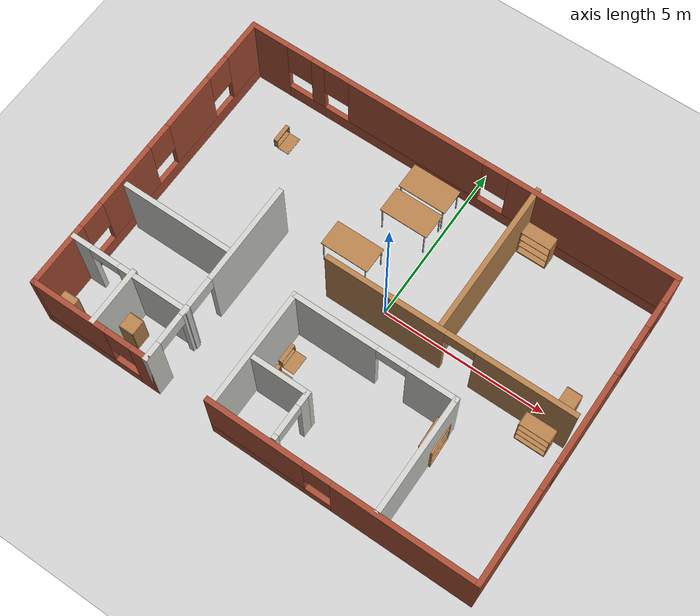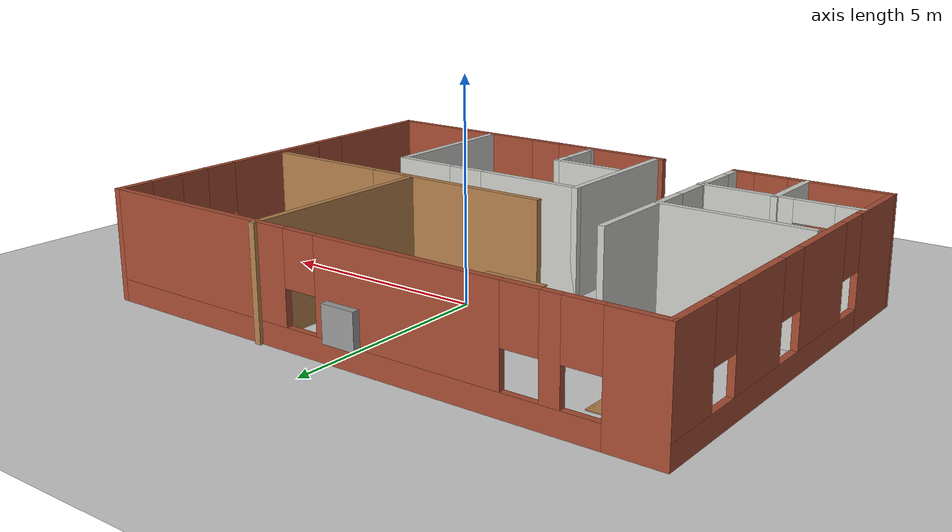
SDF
<sdf version="1.7">
 <world name="default">
  <light name="sun" type="directional">
   <pose>0 0 10 0 -0 0</pose>
   <diffuse>0.8 0.8 0.8 1</diffuse>
   <specular>0.2 0.2 0.2 1</specular>
   <attenuation>
    <range>1000</range>
    <constant>0.9</constant>
    <linear>0.01</linear>
    <quadratic>0.001</quadratic>
   </attenuation>
   <direction>-0.5 0.1 -0.9</direction>
   <spot><inner_angle>0</inner_angle><outer_angle>0</outer_angle><falloff>0</falloff></spot>
  </light>
  <model name="ground_plane">
   <static>1</static>
   <link name="link">
    <collision name="collision">
     <geometry><plane><normal>0 0 1</normal><size>100 100</size></plane></geometry>
     <surface><friction><ode><mu>100</mu><mu2>50</mu2></ode></friction></surface>
    </collision>
    <visual name="visual">
     <cast_shadows>0</cast_shadows>
     <geometry><plane><normal>0 0 1</normal><size>100 100</size></plane></geometry>
     <material>
      <script><uri>file://media/materials/scripts/gazebo.material</uri><name>Gazebo/Grey</name></script>
     </material>
    </visual>
   </link>
  </model>
  <gravity>0 0 -9.8</gravity>
  <magnetic_field>6e-06 2.3e-05 -4.2e-05</magnetic_field>
  <atmosphere type="adiabatic"/>
  <physics type="ode">
   <max_step_size>0.001</max_step_size>
   <real_time_factor>1</real_time_factor>
   <real_time_update_rate>1000</real_time_update_rate>
  </physics>
  <scene><ambient>0.4 0.4 0.4 1</ambient><background>0.7 0.7 0.7 1</background><shadows>1</shadows></scene>
  <audio><device>default</device></audio>
  <spherical_coordinates>
   <surface_model>EARTH_WGS84</surface_model>
   <latitude_deg>0</latitude_deg>
   <longitude_deg>0</longitude_deg>
   <elevation>0</elevation>
   <heading_deg>0</heading_deg>
  </spherical_coordinates>
  <model name="floorplan2">
   <pose>-0.563381 -0.503591 0 0 -0 0</pose>
   <link name="Wall_0">
    <pose>-4.875 -4.71583 0 0 -0 3.14159</pose>
    <visual name="Wall_0_Visual_0">
     <pose>-1.58866 0 1.25 0 -0 0</pose>
     <geometry><box><size>0.572682 0.15 2.5</size></box></geometry>
     <material>
      <script><uri>file://media/materials/scripts/gazebo.material</uri><name>Gazebo/Bricks</name></script>
      <ambient>1 1 1 1</ambient>
     </material>
     <meta><layer>0</layer></meta>
    </visual>
    <collision name="Wall_0_Collision_0">
     <geometry><box><size>0.572682 0.15 2.5</size></box></geometry>
     <pose>-1.58866 0 1.25 0 -0 0</pose>
    </collision>
    <visual name="Wall_0_Visual_1">
     <pose>0.286341 0 0.25 0 -0 0</pose>
     <geometry><box><size>3.17732 0.15 0.5</size></box></geometry>
     <material>
      <script><uri>file://media/materials/scripts/gazebo.material</uri><name>Gazebo/Bricks</name></script>
      <ambient>1 1 1 1</ambient>
     </material>
     <meta><layer>0</layer></meta>
    </visual>
    <collision name="Wall_0_Collision_1">
     <geometry><box><size>3.17732 0.15 0.5</size></box></geometry>
     <pose>0.286341 0 0.25 0 -0 0</pose>
    </collision>
    <visual name="Wall_0_Visual_2">
     <pose>0.686341 0 1.5 0 -0 0</pose>
     <geometry><box><size>2.37732 0.15 2</size></box></geometry>
     <material>
      <script><uri>file://media/materials/scripts/gazebo.material</uri><name>Gazebo/Bricks</name></script>
      <ambient>1 1 1 1</ambient>
     </material>
     <meta><layer>0</layer></meta>
    </visual>
    <collision name="Wall_0_Collision_2">
     <geometry><box><size>2.37732 0.15 2</size></box></geometry>
     <pose>0.686341 0 1.5 0 -0 0</pose>
    </collision>
    <visual name="Wall_0_Visual_3">
     <pose>-0.902318 0 1.9 0 -0 0</pose>
     <geometry><box><size>0.8 0.15 1.2</size></box></geometry>
     <material>
      <script><uri>file://media/materials/scripts/gazebo.material</uri><name>Gazebo/Bricks</name></script>
      <ambient>1 1 1 1</ambient>
     </material>
     <meta><layer>0</layer></meta>
    </visual>
    <collision name="Wall_0_Collision_3">
     <geometry><box><size>0.8 0.15 1.2</size></box></geometry>
     <pose>-0.902318 0 1.9 0 -0 0</pose>
    </collision>
   </link>
   <link name="Wall_1">
    <pose>-6.675 -0.040833 0 0 -0 1.5708</pose>
    <visual name="Wall_1_Visual_0">
     <pose>-3.77003 0 1.25 0 -0 0</pose>
     <geometry><box><size>1.95995 0.15 2.5</size></box></geometry>
     <material>
      <script><uri>file://media/materials/scripts/gazebo.material</uri><name>Gazebo/Bricks</name></script>
      <ambient>1 1 1 1</ambient>
     </material>
     <meta><layer>0</layer></meta>
    </visual>
    <collision name="Wall_1_Collision_0">
     <geometry><box><size>1.95995 0.15 2.5</size></box></geometry>
     <pose>-3.77003 0 1.25 0 -0 0</pose>
    </collision>
    <visual name="Wall_1_Visual_1">
     <pose>0.979973 0 0.25 0 -0 0</pose>
     <geometry><box><size>7.54005 0.15 0.5</size></box></geometry>
     <material>
      <script><uri>file://media/materials/scripts/gazebo.material</uri><name>Gazebo/Bricks</name></script>
      <ambient>1 1 1 1</ambient>
     </material>
     <meta><layer>0</layer></meta>
    </visual>
    <collision name="Wall_1_Collision_1">
     <geometry><box><size>7.54005 0.15 0.5</size></box></geometry>
     <pose>0.979973 0 0.25 0 -0 0</pose>
    </collision>
    <visual name="Wall_1_Visual_2">
     <pose>-0.987882 0 1.5 0 -0 0</pose>
     <geometry><box><size>2.00434 0.15 2</size></box></geometry>
     <material>
      <script><uri>file://media/materials/scripts/gazebo.material</uri><name>Gazebo/Bricks</name></script>
      <ambient>1 1 1 1</ambient>
     </material>
     <meta><layer>0</layer></meta>
    </visual>
    <collision name="Wall_1_Collision_2">
     <geometry><box><size>2.00434 0.15 2</size></box></geometry>
     <pose>-0.987882 0 1.5 0 -0 0</pose>
    </collision>
    <visual name="Wall_1_Visual_3">
     <pose>1.70516 0 1.5 0 -0 0</pose>
     <geometry><box><size>1.78173 0.15 2</size></box></geometry>
     <material>
      <script><uri>file://media/materials/scripts/gazebo.material</uri><name>Gazebo/Bricks</name></script>
      <ambient>1 1 1 1</ambient>
     </material>
     <meta><layer>0</layer></meta>
    </visual>
    <collision name="Wall_1_Collision_3">
     <geometry><box><size>1.78173 0.15 2</size></box></geometry>
     <pose>1.70516 0 1.5 0 -0 0</pose>
    </collision>
    <visual name="Wall_1_Visual_4">
     <pose>4.07301 0 1.5 0 -0 0</pose>
     <geometry><box><size>1.35398 0.15 2</size></box></geometry>
     <material>
      <script><uri>file://media/materials/scripts/gazebo.material</uri><name>Gazebo/Bricks</name></script>
      <ambient>1 1 1 1</ambient>
     </material>
     <meta><layer>0</layer></meta>
    </visual>
    <collision name="Wall_1_Collision_4">
     <geometry><box><size>1.35398 0.15 2</size></box></geometry>
     <pose>4.07301 0 1.5 0 -0 0</pose>
    </collision>
    <visual name="Wall_1_Visual_5">
     <pose>-2.39005 0 1.9 0 -0 0</pose>
     <geometry><box><size>0.8 0.15 1.2</size></box></geometry>
     <material>
      <script><uri>file://media/materials/scripts/gazebo.material</uri><name>Gazebo/Bricks</name></script>
      <ambient>1 1 1 1</ambient>
     </material>
     <meta><layer>0</layer></meta>
    </visual>
    <collision name="Wall_1_Collision_5">
     <geometry><box><size>0.8 0.15 1.2</size></box></geometry>
     <pose>-2.39005 0 1.9 0 -0 0</pose>
    </collision>
    <visual name="Wall_1_Visual_6">
     <pose>0.41429 0 1.9 0 -0 0</pose>
     <geometry><box><size>0.8 0.15 1.2</size></box></geometry>
     <material>
      <script><uri>file://media/materials/scripts/gazebo.material</uri><name>Gazebo/Bricks</name></script>
      <ambient>1 1 1 1</ambient>
     </material>
     <meta><layer>0</layer></meta>
    </visual>
    <collision name="Wall_1_Collision_6">
     <geometry><box><size>0.8 0.15 1.2</size></box></geometry>
     <pose>0.41429 0 1.9 0 -0 0</pose>
    </collision>
    <visual name="Wall_1_Visual_7">
     <pose>2.99602 0 1.9 0 -0 0</pose>
     <geometry><box><size>0.8 0.15 1.2</size></box></geometry>
     <material>
      <script><uri>file://media/materials/scripts/gazebo.material</uri><name>Gazebo/Bricks</name></script>
      <ambient>1 1 1 1</ambient>
     </material>
     <meta><layer>0</layer></meta>
    </visual>
    <collision name="Wall_1_Collision_7">
     <geometry><box><size>0.8 0.15 1.2</size></box></geometry>
     <pose>2.99602 0 1.9 0 -0 0</pose>
    </collision>
   </link>
   <link name="Wall_11">
    <pose>1.37216 -1.26136 0 0 -0 0</pose>
    <visual name="Wall_11_Visual_0">
     <pose>-1.2012 0 1.25 0 -0 0</pose>
     <geometry><box><size>2.59761 0.15 2.5</size></box></geometry>
     <material>
      <script><uri>file://media/materials/scripts/gazebo.material</uri><name>Gazebo/CeilingTiled</name></script>
      <ambient>1 1 1 1</ambient>
     </material>
     <meta><layer>0</layer></meta>
    </visual>
    <collision name="Wall_11_Collision_0">
     <geometry><box><size>2.59761 0.15 2.5</size></box></geometry>
     <pose>-1.2012 0 1.25 0 -0 0</pose>
    </collision>
    <visual name="Wall_11_Visual_1">
     <pose>1.7488 0 1.25 0 -0 0</pose>
     <geometry><box><size>1.50239 0.15 2.5</size></box></geometry>
     <material>
      <script><uri>file://media/materials/scripts/gazebo.material</uri><name>Gazebo/CeilingTiled</name></script>
      <ambient>1 1 1 1</ambient>
     </material>
     <meta><layer>0</layer></meta>
    </visual>
    <collision name="Wall_11_Collision_1">
     <geometry><box><size>1.50239 0.15 2.5</size></box></geometry>
     <pose>1.7488 0 1.25 0 -0 0</pose>
    </collision>
    <visual name="Wall_11_Visual_2">
     <pose>0.547606 0 2.25 0 -0 0</pose>
     <geometry><box><size>0.9 0.15 0.5</size></box></geometry>
     <material>
      <script><uri>file://media/materials/scripts/gazebo.material</uri><name>Gazebo/CeilingTiled</name></script>
      <ambient>1 1 1 1</ambient>
     </material>
     <meta><layer>0</layer></meta>
    </visual>
    <collision name="Wall_11_Collision_2">
     <geometry><box><size>0.9 0.15 0.5</size></box></geometry>
     <pose>0.547606 0 2.25 0 -0 0</pose>
    </collision>
   </link>
   <link name="Wall_12">
    <collision name="Wall_12_Collision">
     <geometry><box><size>3.5 0.15 2.5</size></box></geometry>
     <pose>0 0 1.25 0 -0 0</pose>
    </collision>
    <visual name="Wall_12_Visual">
     <pose>0 0 1.25 0 -0 0</pose>
     <geometry><box><size>3.5 0.15 2.5</size></box></geometry>
     <material>
      <script><uri>file://media/materials/scripts/gazebo.material</uri><name>Gazebo/CeilingTiled</name></script>
      <ambient>1 1 1 1</ambient>
     </material>
     <meta><layer>0</layer></meta>
    </visual>
    <pose>3.79716 -2.93636 0 0 -0 -1.5708</pose>
   </link>
   <link name="Wall_14">
    <pose>-3.075 -1.91583 0 0 -0 1.5708</pose>
    <visual name="Wall_14_Visual_0">
     <pose>-2.59122 0 1.25 0 -0 0</pose>
     <geometry><box><size>0.567569 0.15 2.5</size></box></geometry>
     <material>
      <script><uri>file://media/materials/scripts/gazebo.material</uri><name>Gazebo/CeilingTiled</name></script>
      <ambient>1 1 1 1</ambient>
     </material>
     <meta><layer>0</layer></meta>
    </visual>
    <collision name="Wall_14_Collision_0">
     <geometry><box><size>0.567569 0.15 2.5</size></box></geometry>
     <pose>-2.59122 0 1.25 0 -0 0</pose>
    </collision>
    <visual name="Wall_14_Visual_1">
     <pose>-1.25629 0 1.25 0 -0 0</pose>
     <geometry><box><size>0.302276 0.15 2.5</size></box></geometry>
     <material>
      <script><uri>file://media/materials/scripts/gazebo.material</uri><name>Gazebo/CeilingTiled</name></script>
      <ambient>1 1 1 1</ambient>
     </material>
     <meta><layer>0</layer></meta>
    </visual>
    <collision name="Wall_14_Collision_1">
     <geometry><box><size>0.302276 0.15 2.5</size></box></geometry>
     <pose>-1.25629 0 1.25 0 -0 0</pose>
    </collision>
    <visual name="Wall_14_Visual_2">
     <pose>1.33492 0 1.25 0 -0 0</pose>
     <geometry><box><size>3.08015 0.15 2.5</size></box></geometry>
     <material>
      <script><uri>file://media/materials/scripts/gazebo.material</uri><name>Gazebo/CeilingTiled</name></script>
      <ambient>1 1 1 1</ambient>
     </material>
     <meta><layer>0</layer></meta>
    </visual>
    <collision name="Wall_14_Collision_2">
     <geometry><box><size>3.08015 0.15 2.5</size></box></geometry>
     <pose>1.33492 0 1.25 0 -0 0</pose>
    </collision>
    <visual name="Wall_14_Visual_3">
     <pose>-1.85743 0 2.25 0 -0 0</pose>
     <geometry><box><size>0.9 0.15 0.5</size></box></geometry>
     <material>
      <script><uri>file://media/materials/scripts/gazebo.material</uri><name>Gazebo/CeilingTiled</name></script>
      <ambient>1 1 1 1</ambient>
     </material>
     <meta><layer>0</layer></meta>
    </visual>
    <collision name="Wall_14_Collision_3">
     <geometry><box><size>0.9 0.15 0.5</size></box></geometry>
     <pose>-1.85743 0 2.25 0 -0 0</pose>
    </collision>
    <visual name="Wall_14_Visual_4">
     <pose>-0.655155 0 2.25 0 -0 0</pose>
     <geometry><box><size>0.9 0.15 0.5</size></box></geometry>
     <material>
      <script><uri>file://media/materials/scripts/gazebo.material</uri><name>Gazebo/CeilingTiled</name></script>
      <ambient>1 1 1 1</ambient>
     </material>
     <meta><layer>0</layer></meta>
    </visual>
    <collision name="Wall_14_Collision_4">
     <geometry><box><size>0.9 0.15 0.5</size></box></geometry>
     <pose>-0.655155 0 2.25 0 -0 0</pose>
    </collision>
   </link>
   <link name="Wall_16">
    <collision name="Wall_16_Collision">
     <geometry><box><size>3.5 0.15 2.5</size></box></geometry>
     <pose>0 0 1.25 0 -0 0</pose>
    </collision>
    <visual name="Wall_16_Visual">
     <pose>0 0 1.25 0 -0 0</pose>
     <geometry><box><size>3.5 0.15 2.5</size></box></geometry>
     <material>
      <script><uri>file://media/materials/scripts/gazebo.material</uri><name>Gazebo/CeilingTiled</name></script>
      <ambient>1 1 1 1</ambient>
     </material>
     <meta><layer>0</layer></meta>
    </visual>
    <pose>-4.76821 -1.2166 0 0 -0 3.14159</pose>
   </link>
   <link name="Wall_18">
    <pose>-4.84044 -3.15144 0 0 -0 3.14159</pose>
    <visual name="Wall_18_Visual_0">
     <pose>-0.760886 0 1.25 0 -0 0</pose>
     <geometry><box><size>2.22823 0.15 2.5</size></box></geometry>
     <material>
      <script><uri>file://media/materials/scripts/gazebo.material</uri><name>Gazebo/CeilingTiled</name></script>
      <ambient>1 1 1 1</ambient>
     </material>
     <meta><layer>0</layer></meta>
    </visual>
    <collision name="Wall_18_Collision_0">
     <geometry><box><size>2.22823 0.15 2.5</size></box></geometry>
     <pose>-0.760886 0 1.25 0 -0 0</pose>
    </collision>
    <visual name="Wall_18_Visual_1">
     <pose>1.56411 0 1.25 0 -0 0</pose>
     <geometry><box><size>0.621771 0.15 2.5</size></box></geometry>
     <material>
      <script><uri>file://media/materials/scripts/gazebo.material</uri><name>Gazebo/CeilingTiled</name></script>
      <ambient>1 1 1 1</ambient>
     </material>
     <meta><layer>0</layer></meta>
    </visual>
    <collision name="Wall_18_Collision_1">
     <geometry><box><size>0.621771 0.15 2.5</size></box></geometry>
     <pose>1.56411 0 1.25 0 -0 0</pose>
    </collision>
    <visual name="Wall_18_Visual_2">
     <pose>0.803229 0 2.25 0 -0 0</pose>
     <geometry><box><size>0.9 0.15 0.5</size></box></geometry>
     <material>
      <script><uri>file://media/materials/scripts/gazebo.material</uri><name>Gazebo/CeilingTiled</name></script>
      <ambient>1 1 1 1</ambient>
     </material>
     <meta><layer>0</layer></meta>
    </visual>
    <collision name="Wall_18_Collision_2">
     <geometry><box><size>0.9 0.15 0.5</size></box></geometry>
     <pose>0.803229 0 2.25 0 -0 0</pose>
    </collision>
   </link>
   <link name="Wall_2">
    <pose>-0 4.63417 0 0 -0 0</pose>
    <visual name="Wall_2_Visual_0">
     <pose>-6.1235 0 1.25 0 -0 0</pose>
     <geometry><box><size>1.25301 0.15 2.5</size></box></geometry>
     <material>
      <script><uri>file://media/materials/scripts/gazebo.material</uri><name>Gazebo/Bricks</name></script>
      <ambient>1 1 1 1</ambient>
     </material>
     <meta><layer>0</layer></meta>
    </visual>
    <collision name="Wall_2_Collision_0">
     <geometry><box><size>1.25301 0.15 2.5</size></box></geometry>
     <pose>-6.1235 0 1.25 0 -0 0</pose>
    </collision>
    <visual name="Wall_2_Visual_1">
     <pose>0.626503 0 0.25 0 -0 0</pose>
     <geometry><box><size>12.247 0.15 0.5</size></box></geometry>
     <material>
      <script><uri>file://media/materials/scripts/gazebo.material</uri><name>Gazebo/Bricks</name></script>
      <ambient>1 1 1 1</ambient>
     </material>
     <meta><layer>0</layer></meta>
    </visual>
    <collision name="Wall_2_Collision_1">
     <geometry><box><size>12.247 0.15 0.5</size></box></geometry>
     <pose>0.626503 0 0.25 0 -0 0</pose>
    </collision>
    <visual name="Wall_2_Visual_2">
     <pose>-4.48199 0 1.5 0 -0 0</pose>
     <geometry><box><size>0.43 0.15 2</size></box></geometry>
     <material>
      <script><uri>file://media/materials/scripts/gazebo.material</uri><name>Gazebo/Bricks</name></script>
      <ambient>1 1 1 1</ambient>
     </material>
     <meta><layer>0</layer></meta>
    </visual>
    <collision name="Wall_2_Collision_2">
     <geometry><box><size>0.43 0.15 2</size></box></geometry>
     <pose>-4.48199 0 1.5 0 -0 0</pose>
    </collision>
    <visual name="Wall_2_Visual_3">
     <pose>-1.31329 0 1.5 0 -0 0</pose>
     <geometry><box><size>4.30742 0.15 2</size></box></geometry>
     <material>
      <script><uri>file://media/materials/scripts/gazebo.material</uri><name>Gazebo/Bricks</name></script>
      <ambient>1 1 1 1</ambient>
     </material>
     <meta><layer>0</layer></meta>
    </visual>
    <collision name="Wall_2_Collision_3">
     <geometry><box><size>4.30742 0.15 2</size></box></geometry>
     <pose>-1.31329 0 1.5 0 -0 0</pose>
    </collision>
    <visual name="Wall_2_Visual_4">
     <pose>4.19521 0 1.5 0 -0 0</pose>
     <geometry><box><size>5.10958 0.15 2</size></box></geometry>
     <material>
      <script><uri>file://media/materials/scripts/gazebo.material</uri><name>Gazebo/Bricks</name></script>
      <ambient>1 1 1 1</ambient>
     </material>
     <meta><layer>0</layer></meta>
    </visual>
    <collision name="Wall_2_Collision_4">
     <geometry><box><size>5.10958 0.15 2</size></box></geometry>
     <pose>4.19521 0 1.5 0 -0 0</pose>
    </collision>
    <visual name="Wall_2_Visual_5">
     <pose>-5.09699 0 1.9 0 -0 0</pose>
     <geometry><box><size>0.8 0.15 1.2</size></box></geometry>
     <material>
      <script><uri>file://media/materials/scripts/gazebo.material</uri><name>Gazebo/Bricks</name></script>
      <ambient>1 1 1 1</ambient>
     </material>
     <meta><layer>0</layer></meta>
    </visual>
    <collision name="Wall_2_Collision_5">
     <geometry><box><size>0.8 0.15 1.2</size></box></geometry>
     <pose>-5.09699 0 1.9 0 -0 0</pose>
    </collision>
    <visual name="Wall_2_Visual_6">
     <pose>-3.86699 0 1.9 0 -0 0</pose>
     <geometry><box><size>0.8 0.15 1.2</size></box></geometry>
     <material>
      <script><uri>file://media/materials/scripts/gazebo.material</uri><name>Gazebo/Bricks</name></script>
      <ambient>1 1 1 1</ambient>
     </material>
     <meta><layer>0</layer></meta>
    </visual>
    <collision name="Wall_2_Collision_6">
     <geometry><box><size>0.8 0.15 1.2</size></box></geometry>
     <pose>-3.86699 0 1.9 0 -0 0</pose>
    </collision>
    <visual name="Wall_2_Visual_7">
     <pose>1.24042 0 1.9 0 -0 0</pose>
     <geometry><box><size>0.8 0.15 1.2</size></box></geometry>
     <material>
      <script><uri>file://media/materials/scripts/gazebo.material</uri><name>Gazebo/Bricks</name></script>
      <ambient>1 1 1 1</ambient>
     </material>
     <meta><layer>0</layer></meta>
    </visual>
    <collision name="Wall_2_Collision_7">
     <geometry><box><size>0.8 0.15 1.2</size></box></geometry>
     <pose>1.24042 0 1.9 0 -0 0</pose>
    </collision>
   </link>
   <link name="Wall_26">
    <collision name="Wall_26_Collision">
     <geometry><box><size>3.5 0.15 2.5</size></box></geometry>
     <pose>0 0 1.25 0 -0 0</pose>
    </collision>
    <visual name="Wall_26_Visual">
     <pose>0 0 1.25 0 -0 0</pose>
     <geometry><box><size>3.5 0.15 2.5</size></box></geometry>
     <material>
      <script><uri>file://media/materials/scripts/gazebo.material</uri><name>Gazebo/CeilingTiled</name></script>
      <ambient>1 1 1 1</ambient>
     </material>
     <meta><layer>0</layer></meta>
    </visual>
    <pose>-1.05284 -2.93636 0 0 -0 -1.5708</pose>
   </link>
   <link name="Wall_29">
    <pose>2.75 -4.71583 0 0 -0 3.14159</pose>
    <visual name="Wall_29_Visual_0">
     <pose>-1.87283 0 1.25 0 -0 0</pose>
     <geometry><box><size>4.25434 0.15 2.5</size></box></geometry>
     <material>
      <script><uri>file://media/materials/scripts/gazebo.material</uri><name>Gazebo/Bricks</name></script>
      <ambient>1 1 1 1</ambient>
     </material>
     <meta><layer>0</layer></meta>
    </visual>
    <collision name="Wall_29_Collision_0">
     <geometry><box><size>4.25434 0.15 2.5</size></box></geometry>
     <pose>-1.87283 0 1.25 0 -0 0</pose>
    </collision>
    <visual name="Wall_29_Visual_1">
     <pose>2.12717 0 0.25 0 -0 0</pose>
     <geometry><box><size>3.74566 0.15 0.5</size></box></geometry>
     <material>
      <script><uri>file://media/materials/scripts/gazebo.material</uri><name>Gazebo/Bricks</name></script>
      <ambient>1 1 1 1</ambient>
     </material>
     <meta><layer>0</layer></meta>
    </visual>
    <collision name="Wall_29_Collision_1">
     <geometry><box><size>3.74566 0.15 0.5</size></box></geometry>
     <pose>2.12717 0 0.25 0 -0 0</pose>
    </collision>
    <visual name="Wall_29_Visual_2">
     <pose>2.52717 0 1.5 0 -0 0</pose>
     <geometry><box><size>2.94565 0.15 2</size></box></geometry>
     <material>
      <script><uri>file://media/materials/scripts/gazebo.material</uri><name>Gazebo/Bricks</name></script>
      <ambient>1 1 1 1</ambient>
     </material>
     <meta><layer>0</layer></meta>
    </visual>
    <collision name="Wall_29_Collision_2">
     <geometry><box><size>2.94565 0.15 2</size></box></geometry>
     <pose>2.52717 0 1.5 0 -0 0</pose>
    </collision>
    <visual name="Wall_29_Visual_3">
     <pose>0.654345 0 1.9 0 -0 0</pose>
     <geometry><box><size>0.8 0.15 1.2</size></box></geometry>
     <material>
      <script><uri>file://media/materials/scripts/gazebo.material</uri><name>Gazebo/Bricks</name></script>
      <ambient>1 1 1 1</ambient>
     </material>
     <meta><layer>0</layer></meta>
    </visual>
    <collision name="Wall_29_Collision_3">
     <geometry><box><size>0.8 0.15 1.2</size></box></geometry>
     <pose>0.654345 0 1.9 0 -0 0</pose>
    </collision>
   </link>
   <link name="Wall_3">
    <pose>6.675 -0.040833 0 0 -0 -1.5708</pose>
    <visual name="Wall_3_Visual_0">
     <pose>-4.31623 0 1.25 0 -0 0</pose>
     <geometry><box><size>0.867546 0.15 2.5</size></box></geometry>
     <material>
      <script><uri>file://media/materials/scripts/gazebo.material</uri><name>Gazebo/Bricks</name></script>
      <ambient>1 1 1 1</ambient>
     </material>
     <meta><layer>0</layer></meta>
    </visual>
    <collision name="Wall_3_Collision_0">
     <geometry><box><size>0.867546 0.15 2.5</size></box></geometry>
     <pose>-4.31623 0 1.25 0 -0 0</pose>
    </collision>
    <visual name="Wall_3_Visual_1">
     <pose>0.433773 0 0.25 0 -0 0</pose>
     <geometry><box><size>8.63245 0.15 0.5</size></box></geometry>
     <material>
      <script><uri>file://media/materials/scripts/gazebo.material</uri><name>Gazebo/Bricks</name></script>
      <ambient>1 1 1 1</ambient>
     </material>
     <meta><layer>0</layer></meta>
    </visual>
    <collision name="Wall_3_Collision_1">
     <geometry><box><size>8.63245 0.15 0.5</size></box></geometry>
     <pose>0.433773 0 0.25 0 -0 0</pose>
    </collision>
    <visual name="Wall_3_Visual_2">
     <pose>-2.71941 0 1.5 0 -0 0</pose>
     <geometry><box><size>0.726087 0.15 2</size></box></geometry>
     <material>
      <script><uri>file://media/materials/scripts/gazebo.material</uri><name>Gazebo/Bricks</name></script>
      <ambient>1 1 1 1</ambient>
     </material>
     <meta><layer>0</layer></meta>
    </visual>
    <collision name="Wall_3_Collision_2">
     <geometry><box><size>0.726087 0.15 2</size></box></geometry>
     <pose>-2.71941 0 1.5 0 -0 0</pose>
    </collision>
    <visual name="Wall_3_Visual_3">
     <pose>-0.193453 0 1.5 0 -0 0</pose>
     <geometry><box><size>2.72583 0.15 2</size></box></geometry>
     <material>
      <script><uri>file://media/materials/scripts/gazebo.material</uri><name>Gazebo/Bricks</name></script>
      <ambient>1 1 1 1</ambient>
     </material>
     <meta><layer>0</layer></meta>
    </visual>
    <collision name="Wall_3_Collision_3">
     <geometry><box><size>2.72583 0.15 2</size></box></geometry>
     <pose>-0.193453 0 1.5 0 -0 0</pose>
    </collision>
    <visual name="Wall_3_Visual_4">
     <pose>3.35973 0 1.5 0 -0 0</pose>
     <geometry><box><size>2.78054 0.15 2</size></box></geometry>
     <material>
      <script><uri>file://media/materials/scripts/gazebo.material</uri><name>Gazebo/Bricks</name></script>
      <ambient>1 1 1 1</ambient>
     </material>
     <meta><layer>0</layer></meta>
    </visual>
    <collision name="Wall_3_Collision_4">
     <geometry><box><size>2.78054 0.15 2</size></box></geometry>
     <pose>3.35973 0 1.5 0 -0 0</pose>
    </collision>
    <visual name="Wall_3_Visual_5">
     <pose>-3.48245 0 1.9 0 -0 0</pose>
     <geometry><box><size>0.8 0.15 1.2</size></box></geometry>
     <material>
      <script><uri>file://media/materials/scripts/gazebo.material</uri><name>Gazebo/Bricks</name></script>
      <ambient>1 1 1 1</ambient>
     </material>
     <meta><layer>0</layer></meta>
    </visual>
    <collision name="Wall_3_Collision_5">
     <geometry><box><size>0.8 0.15 1.2</size></box></geometry>
     <pose>-3.48245 0 1.9 0 -0 0</pose>
    </collision>
    <visual name="Wall_3_Visual_6">
     <pose>-1.95637 0 1.9 0 -0 0</pose>
     <geometry><box><size>0.8 0.15 1.2</size></box></geometry>
     <material>
      <script><uri>file://media/materials/scripts/gazebo.material</uri><name>Gazebo/Bricks</name></script>
      <ambient>1 1 1 1</ambient>
     </material>
     <meta><layer>0</layer></meta>
    </visual>
    <collision name="Wall_3_Collision_6">
     <geometry><box><size>0.8 0.15 1.2</size></box></geometry>
     <pose>-1.95637 0 1.9 0 -0 0</pose>
    </collision>
    <visual name="Wall_3_Visual_7">
     <pose>1.56946 0 1.9 0 -0 0</pose>
     <geometry><box><size>0.8 0.15 1.2</size></box></geometry>
     <material>
      <script><uri>file://media/materials/scripts/gazebo.material</uri><name>Gazebo/Bricks</name></script>
      <ambient>1 1 1 1</ambient>
     </material>
     <meta><layer>0</layer></meta>
    </visual>
    <collision name="Wall_3_Collision_7">
     <geometry><box><size>0.8 0.15 1.2</size></box></geometry>
     <pose>1.56946 0 1.9 0 -0 0</pose>
    </collision>
   </link>
   <link name="Wall_31">
    <pose>0.723683 -3.866 0 0 -0 1.5708</pose>
    <visual name="Wall_31_Visual_0">
     <pose>-0.682454 0 1.25 0 -0 0</pose>
     <geometry><box><size>0.135092 0.15 2.5</size></box></geometry>
     <material>
      <script><uri>file://media/materials/scripts/gazebo.material</uri><name>Gazebo/CeilingTiled</name></script>
      <ambient>1 1 1 1</ambient>
     </material>
     <meta><layer>0</layer></meta>
    </visual>
    <collision name="Wall_31_Collision_0">
     <geometry><box><size>0.135092 0.15 2.5</size></box></geometry>
     <pose>-0.682454 0 1.25 0 -0 0</pose>
    </collision>
    <visual name="Wall_31_Visual_1">
     <pose>0.517546 0 1.25 0 -0 0</pose>
     <geometry><box><size>0.464908 0.15 2.5</size></box></geometry>
     <material>
      <script><uri>file://media/materials/scripts/gazebo.material</uri><name>Gazebo/CeilingTiled</name></script>
      <ambient>1 1 1 1</ambient>
     </material>
     <meta><layer>0</layer></meta>
    </visual>
    <collision name="Wall_31_Collision_1">
     <geometry><box><size>0.464908 0.15 2.5</size></box></geometry>
     <pose>0.517546 0 1.25 0 -0 0</pose>
    </collision>
    <visual name="Wall_31_Visual_2">
     <pose>-0.164908 0 2.25 0 -0 0</pose>
     <geometry><box><size>0.9 0.15 0.5</size></box></geometry>
     <material>
      <script><uri>file://media/materials/scripts/gazebo.material</uri><name>Gazebo/CeilingTiled</name></script>
      <ambient>1 1 1 1</ambient>
     </material>
     <meta><layer>0</layer></meta>
    </visual>
    <collision name="Wall_31_Collision_2">
     <geometry><box><size>0.9 0.15 0.5</size></box></geometry>
     <pose>-0.164908 0 2.25 0 -0 0</pose>
    </collision>
   </link>
   <link name="Wall_32">
    <collision name="Wall_32_Collision">
     <geometry><box><size>1.75 0.15 2.5</size></box></geometry>
     <pose>0 0 1.25 0 -0 0</pose>
    </collision>
    <visual name="Wall_32_Visual">
     <pose>0 0 1.25 0 -0 0</pose>
     <geometry><box><size>1.75 0.15 2.5</size></box></geometry>
     <material>
      <script><uri>file://media/materials/scripts/gazebo.material</uri><name>Gazebo/CeilingTiled</name></script>
      <ambient>1 1 1 1</ambient>
     </material>
     <meta><layer>0</layer></meta>
    </visual>
    <pose>-0.076317 -3.191 0 0 -0 3.14159</pose>
   </link>
   <link name="Wall_34">
    <pose>2.73005 0.06742 0 0 -0 3.14159</pose>
    <visual name="Wall_34_Visual_0">
     <pose>-2.2753 0 1.25 0 -0 0</pose>
     <geometry><box><size>2.94939 0.15 2.5</size></box></geometry>
     <material>
      <script><uri>file://media/materials/scripts/gazebo.material</uri><name>Gazebo/Wood</name></script>
      <ambient>1 1 1 1</ambient>
     </material>
     <meta><layer>0</layer></meta>
    </visual>
    <collision name="Wall_34_Collision_0">
     <geometry><box><size>2.94939 0.15 2.5</size></box></geometry>
     <pose>-2.2753 0 1.25 0 -0 0</pose>
    </collision>
    <visual name="Wall_34_Visual_1">
     <pose>1.9247 0 1.25 0 -0 0</pose>
     <geometry><box><size>3.65061 0.15 2.5</size></box></geometry>
     <material>
      <script><uri>file://media/materials/scripts/gazebo.material</uri><name>Gazebo/Wood</name></script>
      <ambient>1 1 1 1</ambient>
     </material>
     <meta><layer>0</layer></meta>
    </visual>
    <collision name="Wall_34_Collision_1">
     <geometry><box><size>3.65061 0.15 2.5</size></box></geometry>
     <pose>1.9247 0 1.25 0 -0 0</pose>
    </collision>
    <visual name="Wall_34_Visual_2">
     <pose>-0.350607 0 2.25 0 -0 0</pose>
     <geometry><box><size>0.9 0.15 0.5</size></box></geometry>
     <material>
      <script><uri>file://media/materials/scripts/gazebo.material</uri><name>Gazebo/Wood</name></script>
      <ambient>1 1 1 1</ambient>
     </material>
     <meta><layer>0</layer></meta>
    </visual>
    <collision name="Wall_34_Collision_2">
     <geometry><box><size>0.9 0.15 0.5</size></box></geometry>
     <pose>-0.350607 0 2.25 0 -0 0</pose>
    </collision>
   </link>
   <link name="Wall_36">
    <collision name="Wall_36_Collision">
     <geometry><box><size>4.75 0.15 2.5</size></box></geometry>
     <pose>0 0 1.25 0 -0 0</pose>
    </collision>
    <visual name="Wall_36_Visual">
     <pose>0 0 1.25 0 -0 0</pose>
     <geometry><box><size>4.75 0.15 2.5</size></box></geometry>
     <material>
      <script><uri>file://media/materials/scripts/gazebo.material</uri><name>Gazebo/Wood</name></script>
      <ambient>1 1 1 1</ambient>
     </material>
     <meta><layer>0</layer></meta>
    </visual>
    <pose>2.41712 2.41583 0 0 -0 -1.5708</pose>
   </link>
   <link name="Wall_38">
    <collision name="Wall_38_Collision">
     <geometry><box><size>1.75 0.15 2.5</size></box></geometry>
     <pose>0 0 1.25 0 -0 0</pose>
    </collision>
    <visual name="Wall_38_Visual">
     <pose>0 0 1.25 0 -0 0</pose>
     <geometry><box><size>1.75 0.15 2.5</size></box></geometry>
     <material>
      <script><uri>file://media/materials/scripts/gazebo.material</uri><name>Gazebo/CeilingTiled</name></script>
      <ambient>1 1 1 1</ambient>
     </material>
     <meta><layer>0</layer></meta>
    </visual>
    <pose>-4.78548 -3.89055 0 0 -0 1.5708</pose>
   </link>
   <link name="Window_7">
    <collision name="Window_7_Collision">
     <geometry><box><size>0.8 0.17 0.8</size></box></geometry>
     <pose>0 0 0.4 0 -0 0</pose>
    </collision>
    <visual name="Window_7_Visual">
     <pose>0 0 0.4 0 -0 0</pose>
     <geometry><box><size>0.8 0.17 0.8</size></box></geometry>
     <material>
      <script><uri>file://media/materials/scripts/gazebo.material</uri><name>Gazebo/Grey</name></script>
     </material>
    </visual>
    <pose>0.101671 4.81568 0.5 0 -0 0</pose>
   </link>
   <static>1</static>
  </model>
  <model name="bookshelf">
   <static>1</static>
   <link name="link">
    <inertial><mass>1</mass></inertial>
    <collision name="back">
     <pose>0 0.005 0.6 0 -0 0</pose>
     <geometry><box><size>0.9 0.01 1.2</size></box></geometry>
    </collision>
    <visual name="visual1">
     <pose>0 0.005 0.6 0 -0 0</pose>
     <geometry><box><size>0.9 0.01 1.2</size></box></geometry>
     <material>
      <script><uri>file://media/materials/scripts/gazebo.material</uri><name>Gazebo/Wood</name></script>
     </material>
    </visual>
    <collision name="left_side">
     <pose>0.45 -0.195 0.6 0 -0 0</pose>
     <geometry><box><size>0.02 0.4 1.2</size></box></geometry>
    </collision>
    <visual name="visual2">
     <pose>0.45 -0.195 0.6 0 -0 0</pose>
     <geometry><box><size>0.02 0.4 1.2</size></box></geometry>
     <material>
      <script><uri>file://media/materials/scripts/gazebo.material</uri><name>Gazebo/Wood</name></script>
     </material>
    </visual>
    <collision name="right_side">
     <pose>-0.45 -0.195 0.6 0 -0 0</pose>
     <geometry><box><size>0.02 0.4 1.2</size></box></geometry>
    </collision>
    <visual name="visual3">
     <pose>-0.45 -0.195 0.6 0 -0 0</pose>
     <geometry><box><size>0.02 0.4 1.2</size></box></geometry>
     <material>
      <script><uri>file://media/materials/scripts/gazebo.material</uri><name>Gazebo/Wood</name></script>
     </material>
    </visual>
    <collision name="bottom">
     <pose>0 -0.195 0.03 0 -0 0</pose>
     <geometry><box><size>0.88 0.4 0.06</size></box></geometry>
    </collision>
    <visual name="visual4">
     <pose>0 -0.195 0.03 0 -0 0</pose>
     <geometry><box><size>0.88 0.4 0.06</size></box></geometry>
     <material>
      <script><uri>file://media/materials/scripts/gazebo.material</uri><name>Gazebo/Wood</name></script>
     </material>
    </visual>
    <collision name="top">
     <pose>0 -0.195 1.19 0 -0 0</pose>
     <geometry><box><size>0.88 0.4 0.02</size></box></geometry>
    </collision>
    <visual name="visual5">
     <pose>0 -0.195 1.19 0 -0 0</pose>
     <geometry><box><size>0.88 0.4 0.02</size></box></geometry>
     <material>
      <script><uri>file://media/materials/scripts/gazebo.material</uri><name>Gazebo/Wood</name></script>
     </material>
    </visual>
    <collision name="low_shelf">
     <pose>0 -0.195 0.43 0 -0 0</pose>
     <geometry><box><size>0.88 0.4 0.02</size></box></geometry>
    </collision>
    <visual name="visual6">
     <pose>0 -0.195 0.43 0 -0 0</pose>
     <geometry><box><size>0.88 0.4 0.02</size></box></geometry>
     <material>
      <script><uri>file://media/materials/scripts/gazebo.material</uri><name>Gazebo/Wood</name></script>
     </material>
    </visual>
    <collision name="high_shelf">
     <pose>0 -0.195 0.8 0 -0 0</pose>
     <geometry><box><size>0.88 0.4 0.02</size></box></geometry>
    </collision>
    <visual name="visual7">
     <pose>0 -0.195 0.8 0 -0 0</pose>
     <geometry><box><size>0.88 0.4 0.02</size></box></geometry>
     <material>
      <script><uri>file://media/materials/scripts/gazebo.material</uri><name>Gazebo/Wood</name></script>
     </material>
    </visual>
   </link>
   <pose>5.17016 -0.607795 0 0 -0 0</pose>
  </model>
  <model name="cabinet">
   <static>1</static>
   <link name="cabinet_bottom_plate">
    <inertial>
     <pose>0 0 -1 0 -0 0</pose>
     <inertia><ixx>2.05</ixx><ixy>0</ixy><ixz>0</ixz><iyy>2.05</iyy><iyz>0</iyz><izz>2.05</izz></inertia>
     <mass>25</mass>
    </inertial>
    <collision name="cabinet_bottom_plate_geom">
     <pose>0 0 0.01 0 -0 0</pose>
     <geometry><box><size>0.45 0.45 0.02</size></box></geometry>
    </collision>
    <visual name="cabinet_bottom_plate_geom_visual">
     <pose>0 0 0.01 0 -0 0</pose>
     <geometry><box><size>0.45 0.45 0.02</size></box></geometry>
     <material>
      <script><uri>file://media/materials/scripts/gazebo.material</uri><name>Gazebo/Wood</name></script>
     </material>
    </visual>
    <collision name="cabinet_bottom_plate_geom_cabinet_back_plate">
     <pose>0.235 0 0.51 0 -0 0</pose>
     <geometry><box><size>0.02 0.45 1.02</size></box></geometry>
    </collision>
    <visual name="cabinet_bottom_plate_geom_cabinet_back_plate_visual">
     <pose>0.235 0 0.51 0 -0 0</pose>
     <geometry><box><size>0.02 0.45 1.02</size></box></geometry>
     <material>
      <script><uri>file://media/materials/scripts/gazebo.material</uri><name>Gazebo/Wood</name></script>
     </material>
    </visual>
    <collision name="cabinet_bottom_plate_geom_cabinet_left_plate">
     <pose>0 0.235 0.51 0 -0 0</pose>
     <geometry><box><size>0.45 0.02 1.02</size></box></geometry>
    </collision>
    <visual name="cabinet_bottom_plate_geom_cabinet_left_plate_visual">
     <pose>0 0.235 0.51 0 -0 0</pose>
     <geometry><box><size>0.45 0.02 1.02</size></box></geometry>
     <material>
      <script><uri>file://media/materials/scripts/gazebo.material</uri><name>Gazebo/Wood</name></script>
     </material>
    </visual>
    <collision name="cabinet_bottom_plate_geom_cabinet_middle_plate">
     <pose>0 0 0.51 0 -0 0</pose>
     <geometry><box><size>0.45 0.45 0.02</size></box></geometry>
    </collision>
    <visual name="cabinet_bottom_plate_geom_cabinet_middle_plate_visual">
     <pose>0 0 0.51 0 -0 0</pose>
     <geometry><box><size>0.45 0.45 0.02</size></box></geometry>
     <material>
      <script><uri>file://media/materials/scripts/gazebo.material</uri><name>Gazebo/Wood</name></script>
     </material>
    </visual>
    <collision name="cabinet_bottom_plate_geom_cabinet_right_plate">
     <pose>0 -0.235 0.51 0 -0 0</pose>
     <geometry><box><size>0.45 0.02 1.02</size></box></geometry>
    </collision>
    <visual name="cabinet_bottom_plate_geom_cabinet_right_plate_visual">
     <pose>0 -0.235 0.51 0 -0 0</pose>
     <geometry><box><size>0.45 0.02 1.02</size></box></geometry>
     <material>
      <script><uri>file://media/materials/scripts/gazebo.material</uri><name>Gazebo/Wood</name></script>
     </material>
    </visual>
    <collision name="cabinet_bottom_plate_geom_cabinet_top_plate">
     <pose>0 0 1.01 0 -0 0</pose>
     <geometry><box><size>0.45 0.45 0.02</size></box></geometry>
    </collision>
    <visual name="cabinet_bottom_plate_geom_cabinet_top_plate_visual">
     <pose>0 0 1.01 0 -0 0</pose>
     <geometry><box><size>0.45 0.45 0.02</size></box></geometry>
     <material>
      <script><uri>file://media/materials/scripts/gazebo.material</uri><name>Gazebo/Wood</name></script>
     </material>
    </visual>
   </link>
   <pose>5.45396 -0.116203 0 0 -0 0</pose>
  </model>
  <model name="cabinet_0">
   <static>1</static>
   <link name="cabinet_bottom_plate">
    <inertial>
     <pose>0 0 -1 0 -0 0</pose>
     <inertia><ixx>2.05</ixx><ixy>0</ixy><ixz>0</ixz><iyy>2.05</iyy><iyz>0</iyz><izz>2.05</izz></inertia>
     <mass>25</mass>
    </inertial>
    <collision name="cabinet_bottom_plate_geom">
     <pose>0 0 0.01 0 -0 0</pose>
     <geometry><box><size>0.45 0.45 0.02</size></box></geometry>
    </collision>
    <visual name="cabinet_bottom_plate_geom_visual">
     <pose>0 0 0.01 0 -0 0</pose>
     <geometry><box><size>0.45 0.45 0.02</size></box></geometry>
     <material>
      <script><uri>file://media/materials/scripts/gazebo.material</uri><name>Gazebo/Wood</name></script>
     </material>
    </visual>
    <collision name="cabinet_bottom_plate_geom_cabinet_back_plate">
     <pose>0.235 0 0.51 0 -0 0</pose>
     <geometry><box><size>0.02 0.45 1.02</size></box></geometry>
    </collision>
    <visual name="cabinet_bottom_plate_geom_cabinet_back_plate_visual">
     <pose>0.235 0 0.51 0 -0 0</pose>
     <geometry><box><size>0.02 0.45 1.02</size></box></geometry>
     <material>
      <script><uri>file://media/materials/scripts/gazebo.material</uri><name>Gazebo/Wood</name></script>
     </material>
    </visual>
    <collision name="cabinet_bottom_plate_geom_cabinet_left_plate">
     <pose>0 0.235 0.51 0 -0 0</pose>
     <geometry><box><size>0.45 0.02 1.02</size></box></geometry>
    </collision>
    <visual name="cabinet_bottom_plate_geom_cabinet_left_plate_visual">
     <pose>0 0.235 0.51 0 -0 0</pose>
     <geometry><box><size>0.45 0.02 1.02</size></box></geometry>
     <material>
      <script><uri>file://media/materials/scripts/gazebo.material</uri><name>Gazebo/Wood</name></script>
     </material>
    </visual>
    <collision name="cabinet_bottom_plate_geom_cabinet_middle_plate">
     <pose>0 0 0.51 0 -0 0</pose>
     <geometry><box><size>0.45 0.45 0.02</size></box></geometry>
    </collision>
    <visual name="cabinet_bottom_plate_geom_cabinet_middle_plate_visual">
     <pose>0 0 0.51 0 -0 0</pose>
     <geometry><box><size>0.45 0.45 0.02</size></box></geometry>
     <material>
      <script><uri>file://media/materials/scripts/gazebo.material</uri><name>Gazebo/Wood</name></script>
     </material>
    </visual>
    <collision name="cabinet_bottom_plate_geom_cabinet_right_plate">
     <pose>0 -0.235 0.51 0 -0 0</pose>
     <geometry><box><size>0.45 0.02 1.02</size></box></geometry>
    </collision>
    <visual name="cabinet_bottom_plate_geom_cabinet_right_plate_visual">
     <pose>0 -0.235 0.51 0 -0 0</pose>
     <geometry><box><size>0.45 0.02 1.02</size></box></geometry>
     <material>
      <script><uri>file://media/materials/scripts/gazebo.material</uri><name>Gazebo/Wood</name></script>
     </material>
    </visual>
    <collision name="cabinet_bottom_plate_geom_cabinet_top_plate">
     <pose>0 0 1.01 0 -0 0</pose>
     <geometry><box><size>0.45 0.45 0.02</size></box></geometry>
    </collision>
    <visual name="cabinet_bottom_plate_geom_cabinet_top_plate_visual">
     <pose>0 0 1.01 0 -0 0</pose>
     <geometry><box><size>0.45 0.45 0.02</size></box></geometry>
     <material>
      <script><uri>file://media/materials/scripts/gazebo.material</uri><name>Gazebo/Wood</name></script>
     </material>
    </visual>
   </link>
   <pose>5.42399 0.376649 0 0 -0 0</pose>
  </model>
  <model name="bookshelf_0">
   <static>1</static>
   <link name="link">
    <inertial><mass>1</mass></inertial>
    <collision name="back">
     <pose>0 0.005 0.6 0 -0 0</pose>
     <geometry><box><size>0.9 0.01 1.2</size></box></geometry>
    </collision>
    <visual name="visual1">
     <pose>0 0.005 0.6 0 -0 0</pose>
     <geometry><box><size>0.9 0.01 1.2</size></box></geometry>
     <material>
      <script><uri>file://media/materials/scripts/gazebo.material</uri><name>Gazebo/Wood</name></script>
     </material>
    </visual>
    <collision name="left_side">
     <pose>0.45 -0.195 0.6 0 -0 0</pose>
     <geometry><box><size>0.02 0.4 1.2</size></box></geometry>
    </collision>
    <visual name="visual2">
     <pose>0.45 -0.195 0.6 0 -0 0</pose>
     <geometry><box><size>0.02 0.4 1.2</size></box></geometry>
     <material>
      <script><uri>file://media/materials/scripts/gazebo.material</uri><name>Gazebo/Wood</name></script>
     </material>
    </visual>
    <collision name="right_side">
     <pose>-0.45 -0.195 0.6 0 -0 0</pose>
     <geometry><box><size>0.02 0.4 1.2</size></box></geometry>
    </collision>
    <visual name="visual3">
     <pose>-0.45 -0.195 0.6 0 -0 0</pose>
     <geometry><box><size>0.02 0.4 1.2</size></box></geometry>
     <material>
      <script><uri>file://media/materials/scripts/gazebo.material</uri><name>Gazebo/Wood</name></script>
     </material>
    </visual>
    <collision name="bottom">
     <pose>0 -0.195 0.03 0 -0 0</pose>
     <geometry><box><size>0.88 0.4 0.06</size></box></geometry>
    </collision>
    <visual name="visual4">
     <pose>0 -0.195 0.03 0 -0 0</pose>
     <geometry><box><size>0.88 0.4 0.06</size></box></geometry>
     <material>
      <script><uri>file://media/materials/scripts/gazebo.material</uri><name>Gazebo/Wood</name></script>
     </material>
    </visual>
    <collision name="top">
     <pose>0 -0.195 1.19 0 -0 0</pose>
     <geometry><box><size>0.88 0.4 0.02</size></box></geometry>
    </collision>
    <visual name="visual5">
     <pose>0 -0.195 1.19 0 -0 0</pose>
     <geometry><box><size>0.88 0.4 0.02</size></box></geometry>
     <material>
      <script><uri>file://media/materials/scripts/gazebo.material</uri><name>Gazebo/Wood</name></script>
     </material>
    </visual>
    <collision name="low_shelf">
     <pose>0 -0.195 0.43 0 -0 0</pose>
     <geometry><box><size>0.88 0.4 0.02</size></box></geometry>
    </collision>
    <visual name="visual6">
     <pose>0 -0.195 0.43 0 -0 0</pose>
     <geometry><box><size>0.88 0.4 0.02</size></box></geometry>
     <material>
      <script><uri>file://media/materials/scripts/gazebo.material</uri><name>Gazebo/Wood</name></script>
     </material>
    </visual>
    <collision name="high_shelf">
     <pose>0 -0.195 0.8 0 -0 0</pose>
     <geometry><box><size>0.88 0.4 0.02</size></box></geometry>
    </collision>
    <visual name="visual7">
     <pose>0 -0.195 0.8 0 -0 0</pose>
     <geometry><box><size>0.88 0.4 0.02</size></box></geometry>
     <material>
      <script><uri>file://media/materials/scripts/gazebo.material</uri><name>Gazebo/Wood</name></script>
     </material>
    </visual>
   </link>
   <pose>2.39567 3.94225 0 0 -0 0</pose>
  </model>
  <model name="table">
   <static>1</static>
   <link name="link">
    <collision name="surface">
     <pose>0 0 1 0 -0 0</pose>
     <geometry><box><size>1.5 0.8 0.03</size></box></geometry>
     <surface><friction><ode><mu>0.6</mu><mu2>0.6</mu2></ode></friction></surface>
    </collision>
    <visual name="visual1">
     <pose>0 0 1 0 -0 0</pose>
     <geometry><box><size>1.5 0.8 0.03</size></box></geometry>
     <material>
      <script><uri>file://media/materials/scripts/gazebo.material</uri><name>Gazebo/Wood</name></script>
     </material>
    </visual>
    <collision name="front_left_leg">
     <pose>0.68 0.38 0.5 0 -0 0</pose>
     <geometry><cylinder><radius>0.02</radius><length>1</length></cylinder></geometry>
    </collision>
    <visual name="front_left_leg">
     <pose>0.68 0.38 0.5 0 -0 0</pose>
     <geometry><cylinder><radius>0.02</radius><length>1</length></cylinder></geometry>
     <material>
      <script><uri>file://media/materials/scripts/gazebo.material</uri><name>Gazebo/Grey</name></script>
     </material>
    </visual>
    <collision name="front_right_leg">
     <pose>0.68 -0.38 0.5 0 -0 0</pose>
     <geometry><cylinder><radius>0.02</radius><length>1</length></cylinder></geometry>
    </collision>
    <visual name="front_right_leg">
     <pose>0.68 -0.38 0.5 0 -0 0</pose>
     <geometry><cylinder><radius>0.02</radius><length>1</length></cylinder></geometry>
     <material>
      <script><uri>file://media/materials/scripts/gazebo.material</uri><name>Gazebo/Grey</name></script>
     </material>
    </visual>
    <collision name="back_right_leg">
     <pose>-0.68 -0.38 0.5 0 -0 0</pose>
     <geometry><cylinder><radius>0.02</radius><length>1</length></cylinder></geometry>
    </collision>
    <visual name="back_right_leg">
     <pose>-0.68 -0.38 0.5 0 -0 0</pose>
     <geometry><cylinder><radius>0.02</radius><length>1</length></cylinder></geometry>
     <material>
      <script><uri>file://media/materials/scripts/gazebo.material</uri><name>Gazebo/Grey</name></script>
     </material>
    </visual>
    <collision name="back_left_leg">
     <pose>-0.68 0.38 0.5 0 -0 0</pose>
     <geometry><cylinder><radius>0.02</radius><length>1</length></cylinder></geometry>
    </collision>
    <visual name="back_left_leg">
     <pose>-0.68 0.38 0.5 0 -0 0</pose>
     <geometry><cylinder><radius>0.02</radius><length>1</length></cylinder></geometry>
     <material>
      <script><uri>file://media/materials/scripts/gazebo.material</uri><name>Gazebo/Grey</name></script>
     </material>
    </visual>
   </link>
   <pose>-1.58266 0.729495 0 0 -0 0</pose>
  </model>
  <model name="table_0">
   <static>1</static>
   <link name="link">
    <collision name="surface">
     <pose>0 0 1 0 -0 0</pose>
     <geometry><box><size>1.5 0.8 0.03</size></box></geometry>
     <surface><friction><ode><mu>0.6</mu><mu2>0.6</mu2></ode></friction></surface>
    </collision>
    <visual name="visual1">
     <pose>0 0 1 0 -0 0</pose>
     <geometry><box><size>1.5 0.8 0.03</size></box></geometry>
     <material>
      <script><uri>file://media/materials/scripts/gazebo.material</uri><name>Gazebo/Wood</name></script>
     </material>
    </visual>
    <collision name="front_left_leg">
     <pose>0.68 0.38 0.5 0 -0 0</pose>
     <geometry><cylinder><radius>0.02</radius><length>1</length></cylinder></geometry>
    </collision>
    <visual name="front_left_leg">
     <pose>0.68 0.38 0.5 0 -0 0</pose>
     <geometry><cylinder><radius>0.02</radius><length>1</length></cylinder></geometry>
     <material>
      <script><uri>file://media/materials/scripts/gazebo.material</uri><name>Gazebo/Grey</name></script>
     </material>
    </visual>
    <collision name="front_right_leg">
     <pose>0.68 -0.38 0.5 0 -0 0</pose>
     <geometry><cylinder><radius>0.02</radius><length>1</length></cylinder></geometry>
    </collision>
    <visual name="front_right_leg">
     <pose>0.68 -0.38 0.5 0 -0 0</pose>
     <geometry><cylinder><radius>0.02</radius><length>1</length></cylinder></geometry>
     <material>
      <script><uri>file://media/materials/scripts/gazebo.material</uri><name>Gazebo/Grey</name></script>
     </material>
    </visual>
    <collision name="back_right_leg">
     <pose>-0.68 -0.38 0.5 0 -0 0</pose>
     <geometry><cylinder><radius>0.02</radius><length>1</length></cylinder></geometry>
    </collision>
    <visual name="back_right_leg">
     <pose>-0.68 -0.38 0.5 0 -0 0</pose>
     <geometry><cylinder><radius>0.02</radius><length>1</length></cylinder></geometry>
     <material>
      <script><uri>file://media/materials/scripts/gazebo.material</uri><name>Gazebo/Grey</name></script>
     </material>
    </visual>
    <collision name="back_left_leg">
     <pose>-0.68 0.38 0.5 0 -0 0</pose>
     <geometry><cylinder><radius>0.02</radius><length>1</length></cylinder></geometry>
    </collision>
    <visual name="back_left_leg">
     <pose>-0.68 0.38 0.5 0 -0 0</pose>
     <geometry><cylinder><radius>0.02</radius><length>1</length></cylinder></geometry>
     <material>
      <script><uri>file://media/materials/scripts/gazebo.material</uri><name>Gazebo/Grey</name></script>
     </material>
    </visual>
   </link>
   <pose>-0.842738 2.45748 0 0 -0 0</pose>
  </model>
  <model name="table_1">
   <static>1</static>
   <link name="link">
    <collision name="surface">
     <pose>0 0 1 0 -0 0</pose>
     <geometry><box><size>1.5 0.8 0.03</size></box></geometry>
     <surface><friction><ode><mu>0.6</mu><mu2>0.6</mu2></ode></friction></surface>
    </collision>
    <visual name="visual1">
     <pose>0 0 1 0 -0 0</pose>
     <geometry><box><size>1.5 0.8 0.03</size></box></geometry>
     <material>
      <script><uri>file://media/materials/scripts/gazebo.material</uri><name>Gazebo/Wood</name></script>
     </material>
    </visual>
    <collision name="front_left_leg">
     <pose>0.68 0.38 0.5 0 -0 0</pose>
     <geometry><cylinder><radius>0.02</radius><length>1</length></cylinder></geometry>
    </collision>
    <visual name="front_left_leg">
     <pose>0.68 0.38 0.5 0 -0 0</pose>
     <geometry><cylinder><radius>0.02</radius><length>1</length></cylinder></geometry>
     <material>
      <script><uri>file://media/materials/scripts/gazebo.material</uri><name>Gazebo/Grey</name></script>
     </material>
    </visual>
    <collision name="front_right_leg">
     <pose>0.68 -0.38 0.5 0 -0 0</pose>
     <geometry><cylinder><radius>0.02</radius><length>1</length></cylinder></geometry>
    </collision>
    <visual name="front_right_leg">
     <pose>0.68 -0.38 0.5 0 -0 0</pose>
     <geometry><cylinder><radius>0.02</radius><length>1</length></cylinder></geometry>
     <material>
      <script><uri>file://media/materials/scripts/gazebo.material</uri><name>Gazebo/Grey</name></script>
     </material>
    </visual>
    <collision name="back_right_leg">
     <pose>-0.68 -0.38 0.5 0 -0 0</pose>
     <geometry><cylinder><radius>0.02</radius><length>1</length></cylinder></geometry>
    </collision>
    <visual name="back_right_leg">
     <pose>-0.68 -0.38 0.5 0 -0 0</pose>
     <geometry><cylinder><radius>0.02</radius><length>1</length></cylinder></geometry>
     <material>
      <script><uri>file://media/materials/scripts/gazebo.material</uri><name>Gazebo/Grey</name></script>
     </material>
    </visual>
    <collision name="back_left_leg">
     <pose>-0.68 0.38 0.5 0 -0 0</pose>
     <geometry><cylinder><radius>0.02</radius><length>1</length></cylinder></geometry>
    </collision>
    <visual name="back_left_leg">
     <pose>-0.68 0.38 0.5 0 -0 0</pose>
     <geometry><cylinder><radius>0.02</radius><length>1</length></cylinder></geometry>
     <material>
      <script><uri>file://media/materials/scripts/gazebo.material</uri><name>Gazebo/Grey</name></script>
     </material>
    </visual>
   </link>
   <pose>-0.836669 3.34338 0 0 -0 0</pose>
  </model>
  <model name="wooden_case">
   <link name="base">
    <pose>0 0 0.024 0 -0 0</pose>
    <inertial>
     <pose>-0.022184 0 0.171592 0 -0 0</pose>
     <mass>3.96264</mass>
     <inertia>
      <ixx>0.213536</ixx>
      <ixy>0</ixy>
      <ixz>0.000779377</ixz>
      <iyy>0.0708943</iyy>
      <iyz>0</iyz>
      <izz>0.154604</izz>
     </inertia>
    </inertial>
    <collision name="collision_back">
     <pose>-0.053975 0 0.1778 0 -0 0</pose>
     <geometry><box><size>0.01905 0.5461 0.3175</size></box></geometry>
     <surface>
      <contact>
       <poissons_ratio>0.347</poissons_ratio>
       <elastic_modulus>8.8e+09</elastic_modulus>
       <ode><kp>100000</kp><kd>100</kd><max_vel>100</max_vel><min_depth>0.001</min_depth></ode>
      </contact>
      <friction>
       <torsional>
        <coefficient>1</coefficient>
        <use_patch_radius>0</use_patch_radius>
        <surface_radius>0.01</surface_radius>
       </torsional>
      </friction>
     </surface>
    </collision>
    <visual name="visual_back">
     <pose>-0.053975 0 0.1778 0 -0 0</pose>
     <geometry><box><size>0.01905 0.5461 0.3175</size></box></geometry>
     <material>
      <script><uri>file://media/materials/scripts/gazebo.material</uri><name>Gazebo/Wood</name></script>
     </material>
    </visual>
    <collision name="collision_bottom">
     <pose>0 0 0.009525 0 -0 0</pose>
     <geometry><box><size>0.127 0.5842 0.01905</size></box></geometry>
     <surface>
      <contact>
       <poissons_ratio>0.347</poissons_ratio>
       <elastic_modulus>8.8e+09</elastic_modulus>
       <ode><kp>100000</kp><kd>100</kd><max_vel>100</max_vel><min_depth>0.001</min_depth></ode>
      </contact>
      <friction>
       <torsional>
        <coefficient>1</coefficient>
        <use_patch_radius>0</use_patch_radius>
        <surface_radius>0.01</surface_radius>
       </torsional>
      </friction>
     </surface>
    </collision>
    <visual name="visual_bottom">
     <pose>0 0 0.009525 0 -0 0</pose>
     <geometry><box><size>0.127 0.5842 0.01905</size></box></geometry>
     <material>
      <script><uri>file://media/materials/scripts/gazebo.material</uri><name>Gazebo/Wood</name></script>
     </material>
    </visual>
    <collision name="collision_top">
     <pose>0 0 0.346075 0 -0 0</pose>
     <geometry><box><size>0.127 0.5842 0.01905</size></box></geometry>
     <surface>
      <contact>
       <poissons_ratio>0.347</poissons_ratio>
       <elastic_modulus>8.8e+09</elastic_modulus>
       <ode><kp>100000</kp><kd>100</kd><max_vel>100</max_vel><min_depth>0.001</min_depth></ode>
      </contact>
      <friction>
       <torsional>
        <coefficient>1</coefficient>
        <use_patch_radius>0</use_patch_radius>
        <surface_radius>0.01</surface_radius>
       </torsional>
      </friction>
     </surface>
    </collision>
    <visual name="visual_top">
     <pose>0 0 0.346075 0 -0 0</pose>
     <geometry><box><size>0.127 0.5842 0.01905</size></box></geometry>
     <material>
      <script><uri>file://media/materials/scripts/gazebo.material</uri><name>Gazebo/Wood</name></script>
     </material>
    </visual>
    <collision name="collision_left">
     <pose>0 -0.282575 0.1778 0 -0 0</pose>
     <geometry><box><size>0.127 0.01905 0.3175</size></box></geometry>
     <surface>
      <contact>
       <poissons_ratio>0.347</poissons_ratio>
       <elastic_modulus>8.8e+09</elastic_modulus>
       <ode><kp>100000</kp><kd>100</kd><max_vel>100</max_vel><min_depth>0.001</min_depth></ode>
      </contact>
      <friction>
       <torsional>
        <coefficient>1</coefficient>
        <use_patch_radius>0</use_patch_radius>
        <surface_radius>0.01</surface_radius>
       </torsional>
      </friction>
     </surface>
    </collision>
    <visual name="visual_left">
     <pose>0 -0.282575 0.1778 0 -0 0</pose>
     <geometry><box><size>0.127 0.01905 0.3175</size></box></geometry>
     <material>
      <script><uri>file://media/materials/scripts/gazebo.material</uri><name>Gazebo/Wood</name></script>
     </material>
    </visual>
    <collision name="collision_right">
     <pose>0 0.282575 0.1778 0 -0 0</pose>
     <geometry><box><size>0.127 0.01905 0.3175</size></box></geometry>
     <surface>
      <contact>
       <poissons_ratio>0.347</poissons_ratio>
       <elastic_modulus>8.8e+09</elastic_modulus>
       <ode><kp>100000</kp><kd>100</kd><max_vel>100</max_vel><min_depth>0.001</min_depth></ode>
      </contact>
      <friction>
       <torsional>
        <coefficient>1</coefficient>
        <use_patch_radius>0</use_patch_radius>
        <surface_radius>0.01</surface_radius>
       </torsional>
      </friction>
     </surface>
    </collision>
    <visual name="visual_right">
     <pose>0 0.282575 0.1778 0 -0 0</pose>
     <geometry><box><size>0.127 0.01905 0.3175</size></box></geometry>
     <material>
      <script><uri>file://media/materials/scripts/gazebo.material</uri><name>Gazebo/Wood</name></script>
     </material>
    </visual>
    <collision name="collision_block_left">
     <pose>0.0095 -0.2151 -0.012 0 -0 0</pose>
     <geometry><box><size>0.108 0.05 0.024</size></box></geometry>
     <surface>
      <contact>
       <poissons_ratio>0.347</poissons_ratio>
       <elastic_modulus>8.8e+09</elastic_modulus>
       <ode><kp>100000</kp><kd>100</kd><max_vel>100</max_vel><min_depth>0.001</min_depth></ode>
      </contact>
      <friction>
       <torsional>
        <coefficient>1</coefficient>
        <use_patch_radius>0</use_patch_radius>
        <surface_radius>0.01</surface_radius>
       </torsional>
      </friction>
     </surface>
    </collision>
    <visual name="visual_block_left">
     <pose>0.0095 -0.2151 -0.012 0 -0 0</pose>
     <geometry><box><size>0.108 0.05 0.024</size></box></geometry>
     <material>
      <script><uri>file://media/materials/scripts/gazebo.material</uri><name>Gazebo/Wood</name></script>
     </material>
    </visual>
    <collision name="collision_block_right">
     <pose>0.0095 0.2151 -0.012 0 -0 0</pose>
     <geometry><box><size>0.108 0.05 0.024</size></box></geometry>
     <surface>
      <contact>
       <poissons_ratio>0.347</poissons_ratio>
       <elastic_modulus>8.8e+09</elastic_modulus>
       <ode><kp>100000</kp><kd>100</kd><max_vel>100</max_vel><min_depth>0.001</min_depth></ode>
      </contact>
      <friction>
       <torsional>
        <coefficient>1</coefficient>
        <use_patch_radius>0</use_patch_radius>
        <surface_radius>0.01</surface_radius>
       </torsional>
      </friction>
     </surface>
    </collision>
    <visual name="visual_block_right">
     <pose>0.0095 0.2151 -0.012 0 -0 0</pose>
     <geometry><box><size>0.108 0.05 0.024</size></box></geometry>
     <material>
      <script><uri>file://media/materials/scripts/gazebo.material</uri><name>Gazebo/Wood</name></script>
     </material>
    </visual>
   </link>
   <link name="lid">
    <pose>0.243775 0 0.009525 0 -0 0</pose>
    <inertial>
     <mass>1.97874</mass>
     <inertia>
      <ixx>0.0563367</ixx>
      <ixy>0</ixy>
      <ixz>0</ixz>
      <iyy>0.020911</iyy>
      <iyz>0</iyz>
      <izz>0.0771281</izz>
     </inertia>
    </inertial>
    <collision name="collision">
     <geometry><box><size>0.3556 0.5842 0.01905</size></box></geometry>
     <surface>
      <contact>
       <poissons_ratio>0.347</poissons_ratio>
       <elastic_modulus>8.8e+09</elastic_modulus>
       <ode><kp>100000</kp><kd>100</kd><max_vel>100</max_vel><min_depth>0.001</min_depth></ode>
      </contact>
      <friction>
       <torsional>
        <coefficient>1</coefficient>
        <use_patch_radius>0</use_patch_radius>
        <surface_radius>0.01</surface_radius>
       </torsional>
      </friction>
     </surface>
    </collision>
    <visual name="visual">
     <geometry><box><size>0.3556 0.5842 0.01905</size></box></geometry>
     <material>
      <script><uri>file://media/materials/scripts/gazebo.material</uri><name>Gazebo/Wood</name></script>
     </material>
    </visual>
    <visual name="tee_nut_1">
     <pose>0.122 -0.216 0 0 -0 0</pose>
     <geometry><cylinder><radius>0.00635</radius><length>0.0192405</length></cylinder></geometry>
     <material>
      <script><uri>file://media/materials/scripts/gazebo.material</uri><name>Gazebo/Grey</name></script>
     </material>
    </visual>
    <visual name="tee_nut_2">
     <pose>0.122 -0.088 0 0 -0 0</pose>
     <geometry><cylinder><radius>0.00635</radius><length>0.0192405</length></cylinder></geometry>
     <material>
      <script><uri>file://media/materials/scripts/gazebo.material</uri><name>Gazebo/Grey</name></script>
     </material>
    </visual>
    <visual name="tee_nut_3">
     <pose>0.122 0.088 0 0 -0 0</pose>
     <geometry><cylinder><radius>0.00635</radius><length>0.0192405</length></cylinder></geometry>
     <material>
      <script><uri>file://media/materials/scripts/gazebo.material</uri><name>Gazebo/Grey</name></script>
     </material>
    </visual>
    <visual name="tee_nut_4">
     <pose>0.122 0.216 0 0 -0 0</pose>
     <geometry><cylinder><radius>0.00635</radius><length>0.0192405</length></cylinder></geometry>
     <material>
      <script><uri>file://media/materials/scripts/gazebo.material</uri><name>Gazebo/Grey</name></script>
     </material>
    </visual>
   </link>
   <joint name="lid_hinge" type="revolute">
    <pose>-0.1778 0 0.01905 0 -0 0</pose>
    <parent>base</parent>
    <child>lid</child>
    <axis>
     <xyz>0 1 0</xyz>
     <limit><upper>0.523599</upper><lower>-1.5708</lower></limit>
     <dynamics><spring_reference>0</spring_reference><spring_stiffness>0</spring_stiffness></dynamics>
    </axis>
   </joint>
   <pose>-5.41069 2.72548 0 0 -0 0</pose>
  </model>
  <model name="cabinet_1">
   <static>1</static>
   <link name="cabinet_bottom_plate">
    <inertial>
     <pose>0 0 -1 0 -0 0</pose>
     <inertia><ixx>2.05</ixx><ixy>0</ixy><ixz>0</ixz><iyy>2.05</iyy><iyz>0</iyz><izz>2.05</izz></inertia>
     <mass>25</mass>
    </inertial>
    <collision name="cabinet_bottom_plate_geom">
     <pose>0 0 0.01 0 -0 0</pose>
     <geometry><box><size>0.45 0.45 0.02</size></box></geometry>
    </collision>
    <visual name="cabinet_bottom_plate_geom_visual">
     <pose>0 0 0.01 0 -0 0</pose>
     <geometry><box><size>0.45 0.45 0.02</size></box></geometry>
     <material>
      <script><uri>file://media/materials/scripts/gazebo.material</uri><name>Gazebo/Wood</name></script>
     </material>
    </visual>
    <collision name="cabinet_bottom_plate_geom_cabinet_back_plate">
     <pose>0.235 0 0.51 0 -0 0</pose>
     <geometry><box><size>0.02 0.45 1.02</size></box></geometry>
    </collision>
    <visual name="cabinet_bottom_plate_geom_cabinet_back_plate_visual">
     <pose>0.235 0 0.51 0 -0 0</pose>
     <geometry><box><size>0.02 0.45 1.02</size></box></geometry>
     <material>
      <script><uri>file://media/materials/scripts/gazebo.material</uri><name>Gazebo/Wood</name></script>
     </material>
    </visual>
    <collision name="cabinet_bottom_plate_geom_cabinet_left_plate">
     <pose>0 0.235 0.51 0 -0 0</pose>
     <geometry><box><size>0.45 0.02 1.02</size></box></geometry>
    </collision>
    <visual name="cabinet_bottom_plate_geom_cabinet_left_plate_visual">
     <pose>0 0.235 0.51 0 -0 0</pose>
     <geometry><box><size>0.45 0.02 1.02</size></box></geometry>
     <material>
      <script><uri>file://media/materials/scripts/gazebo.material</uri><name>Gazebo/Wood</name></script>
     </material>
    </visual>
    <collision name="cabinet_bottom_plate_geom_cabinet_middle_plate">
     <pose>0 0 0.51 0 -0 0</pose>
     <geometry><box><size>0.45 0.45 0.02</size></box></geometry>
    </collision>
    <visual name="cabinet_bottom_plate_geom_cabinet_middle_plate_visual">
     <pose>0 0 0.51 0 -0 0</pose>
     <geometry><box><size>0.45 0.45 0.02</size></box></geometry>
     <material>
      <script><uri>file://media/materials/scripts/gazebo.material</uri><name>Gazebo/Wood</name></script>
     </material>
    </visual>
    <collision name="cabinet_bottom_plate_geom_cabinet_right_plate">
     <pose>0 -0.235 0.51 0 -0 0</pose>
     <geometry><box><size>0.45 0.02 1.02</size></box></geometry>
    </collision>
    <visual name="cabinet_bottom_plate_geom_cabinet_right_plate_visual">
     <pose>0 -0.235 0.51 0 -0 0</pose>
     <geometry><box><size>0.45 0.02 1.02</size></box></geometry>
     <material>
      <script><uri>file://media/materials/scripts/gazebo.material</uri><name>Gazebo/Wood</name></script>
     </material>
    </visual>
    <collision name="cabinet_bottom_plate_geom_cabinet_top_plate">
     <pose>0 0 1.01 0 -0 0</pose>
     <geometry><box><size>0.45 0.45 0.02</size></box></geometry>
    </collision>
    <visual name="cabinet_bottom_plate_geom_cabinet_top_plate_visual">
     <pose>0 0 1.01 0 -0 0</pose>
     <geometry><box><size>0.45 0.45 0.02</size></box></geometry>
     <material>
      <script><uri>file://media/materials/scripts/gazebo.material</uri><name>Gazebo/Wood</name></script>
     </material>
    </visual>
   </link>
   <pose>-6.84809 -4.8686 0 0 -0 0</pose>
  </model>
  <model name="cabinet_2">
   <static>1</static>
   <link name="cabinet_bottom_plate">
    <inertial>
     <pose>0 0 -1 0 -0 0</pose>
     <inertia><ixx>2.05</ixx><ixy>0</ixy><ixz>0</ixz><iyy>2.05</iyy><iyz>0</iyz><izz>2.05</izz></inertia>
     <mass>25</mass>
    </inertial>
    <collision name="cabinet_bottom_plate_geom">
     <pose>0 0 0.01 0 -0 0</pose>
     <geometry><box><size>0.45 0.45 0.02</size></box></geometry>
    </collision>
    <visual name="cabinet_bottom_plate_geom_visual">
     <pose>0 0 0.01 0 -0 0</pose>
     <geometry><box><size>0.45 0.45 0.02</size></box></geometry>
     <material>
      <script><uri>file://media/materials/scripts/gazebo.material</uri><name>Gazebo/Wood</name></script>
     </material>
    </visual>
    <collision name="cabinet_bottom_plate_geom_cabinet_back_plate">
     <pose>0.235 0 0.51 0 -0 0</pose>
     <geometry><box><size>0.02 0.45 1.02</size></box></geometry>
    </collision>
    <visual name="cabinet_bottom_plate_geom_cabinet_back_plate_visual">
     <pose>0.235 0 0.51 0 -0 0</pose>
     <geometry><box><size>0.02 0.45 1.02</size></box></geometry>
     <material>
      <script><uri>file://media/materials/scripts/gazebo.material</uri><name>Gazebo/Wood</name></script>
     </material>
    </visual>
    <collision name="cabinet_bottom_plate_geom_cabinet_left_plate">
     <pose>0 0.235 0.51 0 -0 0</pose>
     <geometry><box><size>0.45 0.02 1.02</size></box></geometry>
    </collision>
    <visual name="cabinet_bottom_plate_geom_cabinet_left_plate_visual">
     <pose>0 0.235 0.51 0 -0 0</pose>
     <geometry><box><size>0.45 0.02 1.02</size></box></geometry>
     <material>
      <script><uri>file://media/materials/scripts/gazebo.material</uri><name>Gazebo/Wood</name></script>
     </material>
    </visual>
    <collision name="cabinet_bottom_plate_geom_cabinet_middle_plate">
     <pose>0 0 0.51 0 -0 0</pose>
     <geometry><box><size>0.45 0.45 0.02</size></box></geometry>
    </collision>
    <visual name="cabinet_bottom_plate_geom_cabinet_middle_plate_visual">
     <pose>0 0 0.51 0 -0 0</pose>
     <geometry><box><size>0.45 0.45 0.02</size></box></geometry>
     <material>
      <script><uri>file://media/materials/scripts/gazebo.material</uri><name>Gazebo/Wood</name></script>
     </material>
    </visual>
    <collision name="cabinet_bottom_plate_geom_cabinet_right_plate">
     <pose>0 -0.235 0.51 0 -0 0</pose>
     <geometry><box><size>0.45 0.02 1.02</size></box></geometry>
    </collision>
    <visual name="cabinet_bottom_plate_geom_cabinet_right_plate_visual">
     <pose>0 -0.235 0.51 0 -0 0</pose>
     <geometry><box><size>0.45 0.02 1.02</size></box></geometry>
     <material>
      <script><uri>file://media/materials/scripts/gazebo.material</uri><name>Gazebo/Wood</name></script>
     </material>
    </visual>
    <collision name="cabinet_bottom_plate_geom_cabinet_top_plate">
     <pose>0 0 1.01 0 -0 0</pose>
     <geometry><box><size>0.45 0.45 0.02</size></box></geometry>
    </collision>
    <visual name="cabinet_bottom_plate_geom_cabinet_top_plate_visual">
     <pose>0 0 1.01 0 -0 0</pose>
     <geometry><box><size>0.45 0.45 0.02</size></box></geometry>
     <material>
      <script><uri>file://media/materials/scripts/gazebo.material</uri><name>Gazebo/Wood</name></script>
     </material>
    </visual>
   </link>
   <pose>-5.06456 -4.3863 0 0 -0 0</pose>
  </model>
  <model name="wooden_case_0">
   <link name="base">
    <pose>0 0 0.024 0 -0 0</pose>
    <inertial>
     <pose>-0.022184 0 0.171592 0 -0 0</pose>
     <mass>3.96264</mass>
     <inertia>
      <ixx>0.213536</ixx>
      <ixy>0</ixy>
      <ixz>0.000779377</ixz>
      <iyy>0.0708943</iyy>
      <iyz>0</iyz>
      <izz>0.154604</izz>
     </inertia>
    </inertial>
    <collision name="collision_back">
     <pose>-0.053975 0 0.1778 0 -0 0</pose>
     <geometry><box><size>0.01905 0.5461 0.3175</size></box></geometry>
     <surface>
      <contact>
       <poissons_ratio>0.347</poissons_ratio>
       <elastic_modulus>8.8e+09</elastic_modulus>
       <ode><kp>100000</kp><kd>100</kd><max_vel>100</max_vel><min_depth>0.001</min_depth></ode>
      </contact>
      <friction>
       <torsional>
        <coefficient>1</coefficient>
        <use_patch_radius>0</use_patch_radius>
        <surface_radius>0.01</surface_radius>
       </torsional>
      </friction>
     </surface>
    </collision>
    <visual name="visual_back">
     <pose>-0.053975 0 0.1778 0 -0 0</pose>
     <geometry><box><size>0.01905 0.5461 0.3175</size></box></geometry>
     <material>
      <script><uri>file://media/materials/scripts/gazebo.material</uri><name>Gazebo/Wood</name></script>
     </material>
    </visual>
    <collision name="collision_bottom">
     <pose>0 0 0.009525 0 -0 0</pose>
     <geometry><box><size>0.127 0.5842 0.01905</size></box></geometry>
     <surface>
      <contact>
       <poissons_ratio>0.347</poissons_ratio>
       <elastic_modulus>8.8e+09</elastic_modulus>
       <ode><kp>100000</kp><kd>100</kd><max_vel>100</max_vel><min_depth>0.001</min_depth></ode>
      </contact>
      <friction>
       <torsional>
        <coefficient>1</coefficient>
        <use_patch_radius>0</use_patch_radius>
        <surface_radius>0.01</surface_radius>
       </torsional>
      </friction>
     </surface>
    </collision>
    <visual name="visual_bottom">
     <pose>0 0 0.009525 0 -0 0</pose>
     <geometry><box><size>0.127 0.5842 0.01905</size></box></geometry>
     <material>
      <script><uri>file://media/materials/scripts/gazebo.material</uri><name>Gazebo/Wood</name></script>
     </material>
    </visual>
    <collision name="collision_top">
     <pose>0 0 0.346075 0 -0 0</pose>
     <geometry><box><size>0.127 0.5842 0.01905</size></box></geometry>
     <surface>
      <contact>
       <poissons_ratio>0.347</poissons_ratio>
       <elastic_modulus>8.8e+09</elastic_modulus>
       <ode><kp>100000</kp><kd>100</kd><max_vel>100</max_vel><min_depth>0.001</min_depth></ode>
      </contact>
      <friction>
       <torsional>
        <coefficient>1</coefficient>
        <use_patch_radius>0</use_patch_radius>
        <surface_radius>0.01</surface_radius>
       </torsional>
      </friction>
     </surface>
    </collision>
    <visual name="visual_top">
     <pose>0 0 0.346075 0 -0 0</pose>
     <geometry><box><size>0.127 0.5842 0.01905</size></box></geometry>
     <material>
      <script><uri>file://media/materials/scripts/gazebo.material</uri><name>Gazebo/Wood</name></script>
     </material>
    </visual>
    <collision name="collision_left">
     <pose>0 -0.282575 0.1778 0 -0 0</pose>
     <geometry><box><size>0.127 0.01905 0.3175</size></box></geometry>
     <surface>
      <contact>
       <poissons_ratio>0.347</poissons_ratio>
       <elastic_modulus>8.8e+09</elastic_modulus>
       <ode><kp>100000</kp><kd>100</kd><max_vel>100</max_vel><min_depth>0.001</min_depth></ode>
      </contact>
      <friction>
       <torsional>
        <coefficient>1</coefficient>
        <use_patch_radius>0</use_patch_radius>
        <surface_radius>0.01</surface_radius>
       </torsional>
      </friction>
     </surface>
    </collision>
    <visual name="visual_left">
     <pose>0 -0.282575 0.1778 0 -0 0</pose>
     <geometry><box><size>0.127 0.01905 0.3175</size></box></geometry>
     <material>
      <script><uri>file://media/materials/scripts/gazebo.material</uri><name>Gazebo/Wood</name></script>
     </material>
    </visual>
    <collision name="collision_right">
     <pose>0 0.282575 0.1778 0 -0 0</pose>
     <geometry><box><size>0.127 0.01905 0.3175</size></box></geometry>
     <surface>
      <contact>
       <poissons_ratio>0.347</poissons_ratio>
       <elastic_modulus>8.8e+09</elastic_modulus>
       <ode><kp>100000</kp><kd>100</kd><max_vel>100</max_vel><min_depth>0.001</min_depth></ode>
      </contact>
      <friction>
       <torsional>
        <coefficient>1</coefficient>
        <use_patch_radius>0</use_patch_radius>
        <surface_radius>0.01</surface_radius>
       </torsional>
      </friction>
     </surface>
    </collision>
    <visual name="visual_right">
     <pose>0 0.282575 0.1778 0 -0 0</pose>
     <geometry><box><size>0.127 0.01905 0.3175</size></box></geometry>
     <material>
      <script><uri>file://media/materials/scripts/gazebo.material</uri><name>Gazebo/Wood</name></script>
     </material>
    </visual>
    <collision name="collision_block_left">
     <pose>0.0095 -0.2151 -0.012 0 -0 0</pose>
     <geometry><box><size>0.108 0.05 0.024</size></box></geometry>
     <surface>
      <contact>
       <poissons_ratio>0.347</poissons_ratio>
       <elastic_modulus>8.8e+09</elastic_modulus>
       <ode><kp>100000</kp><kd>100</kd><max_vel>100</max_vel><min_depth>0.001</min_depth></ode>
      </contact>
      <friction>
       <torsional>
        <coefficient>1</coefficient>
        <use_patch_radius>0</use_patch_radius>
        <surface_radius>0.01</surface_radius>
       </torsional>
      </friction>
     </surface>
    </collision>
    <visual name="visual_block_left">
     <pose>0.0095 -0.2151 -0.012 0 -0 0</pose>
     <geometry><box><size>0.108 0.05 0.024</size></box></geometry>
     <material>
      <script><uri>file://media/materials/scripts/gazebo.material</uri><name>Gazebo/Wood</name></script>
     </material>
    </visual>
    <collision name="collision_block_right">
     <pose>0.0095 0.2151 -0.012 0 -0 0</pose>
     <geometry><box><size>0.108 0.05 0.024</size></box></geometry>
     <surface>
      <contact>
       <poissons_ratio>0.347</poissons_ratio>
       <elastic_modulus>8.8e+09</elastic_modulus>
       <ode><kp>100000</kp><kd>100</kd><max_vel>100</max_vel><min_depth>0.001</min_depth></ode>
      </contact>
      <friction>
       <torsional>
        <coefficient>1</coefficient>
        <use_patch_radius>0</use_patch_radius>
        <surface_radius>0.01</surface_radius>
       </torsional>
      </friction>
     </surface>
    </collision>
    <visual name="visual_block_right">
     <pose>0.0095 0.2151 -0.012 0 -0 0</pose>
     <geometry><box><size>0.108 0.05 0.024</size></box></geometry>
     <material>
      <script><uri>file://media/materials/scripts/gazebo.material</uri><name>Gazebo/Wood</name></script>
     </material>
    </visual>
   </link>
   <link name="lid">
    <pose>0.243775 0 0.009525 0 -0 0</pose>
    <inertial>
     <mass>1.97874</mass>
     <inertia>
      <ixx>0.0563367</ixx>
      <ixy>0</ixy>
      <ixz>0</ixz>
      <iyy>0.020911</iyy>
      <iyz>0</iyz>
      <izz>0.0771281</izz>
     </inertia>
    </inertial>
    <collision name="collision">
     <geometry><box><size>0.3556 0.5842 0.01905</size></box></geometry>
     <surface>
      <contact>
       <poissons_ratio>0.347</poissons_ratio>
       <elastic_modulus>8.8e+09</elastic_modulus>
       <ode><kp>100000</kp><kd>100</kd><max_vel>100</max_vel><min_depth>0.001</min_depth></ode>
      </contact>
      <friction>
       <torsional>
        <coefficient>1</coefficient>
        <use_patch_radius>0</use_patch_radius>
        <surface_radius>0.01</surface_radius>
       </torsional>
      </friction>
     </surface>
    </collision>
    <visual name="visual">
     <geometry><box><size>0.3556 0.5842 0.01905</size></box></geometry>
     <material>
      <script><uri>file://media/materials/scripts/gazebo.material</uri><name>Gazebo/Wood</name></script>
     </material>
    </visual>
    <visual name="tee_nut_1">
     <pose>0.122 -0.216 0 0 -0 0</pose>
     <geometry><cylinder><radius>0.00635</radius><length>0.0192405</length></cylinder></geometry>
     <material>
      <script><uri>file://media/materials/scripts/gazebo.material</uri><name>Gazebo/Grey</name></script>
     </material>
    </visual>
    <visual name="tee_nut_2">
     <pose>0.122 -0.088 0 0 -0 0</pose>
     <geometry><cylinder><radius>0.00635</radius><length>0.0192405</length></cylinder></geometry>
     <material>
      <script><uri>file://media/materials/scripts/gazebo.material</uri><name>Gazebo/Grey</name></script>
     </material>
    </visual>
    <visual name="tee_nut_3">
     <pose>0.122 0.088 0 0 -0 0</pose>
     <geometry><cylinder><radius>0.00635</radius><length>0.0192405</length></cylinder></geometry>
     <material>
      <script><uri>file://media/materials/scripts/gazebo.material</uri><name>Gazebo/Grey</name></script>
     </material>
    </visual>
    <visual name="tee_nut_4">
     <pose>0.122 0.216 0 0 -0 0</pose>
     <geometry><cylinder><radius>0.00635</radius><length>0.0192405</length></cylinder></geometry>
     <material>
      <script><uri>file://media/materials/scripts/gazebo.material</uri><name>Gazebo/Grey</name></script>
     </material>
    </visual>
   </link>
   <joint name="lid_hinge" type="revolute">
    <pose>-0.1778 0 0.01905 0 -0 0</pose>
    <parent>base</parent>
    <child>lid</child>
    <axis>
     <xyz>0 1 0</xyz>
     <limit><upper>0.523599</upper><lower>-1.5708</lower></limit>
     <dynamics><spring_reference>0</spring_reference><spring_stiffness>0</spring_stiffness></dynamics>
    </axis>
   </joint>
   <pose>-1.3734 -3.23289 0 0 -0 0</pose>
  </model>
  <model name="wooden_case_1">
   <link name="base">
    <pose>0 0 0.024 0 -0 0</pose>
    <inertial>
     <pose>-0.022184 0 0.171592 0 -0 0</pose>
     <mass>3.96264</mass>
     <inertia>
      <ixx>0.213536</ixx>
      <ixy>0</ixy>
      <ixz>0.000779377</ixz>
      <iyy>0.0708943</iyy>
      <iyz>0</iyz>
      <izz>0.154604</izz>
     </inertia>
    </inertial>
    <collision name="collision_back">
     <pose>-0.053975 0 0.1778 0 -0 0</pose>
     <geometry><box><size>0.01905 0.5461 0.3175</size></box></geometry>
     <surface>
      <contact>
       <poissons_ratio>0.347</poissons_ratio>
       <elastic_modulus>8.8e+09</elastic_modulus>
       <ode><kp>100000</kp><kd>100</kd><max_vel>100</max_vel><min_depth>0.001</min_depth></ode>
      </contact>
      <friction>
       <torsional>
        <coefficient>1</coefficient>
        <use_patch_radius>0</use_patch_radius>
        <surface_radius>0.01</surface_radius>
       </torsional>
      </friction>
     </surface>
    </collision>
    <visual name="visual_back">
     <pose>-0.053975 0 0.1778 0 -0 0</pose>
     <geometry><box><size>0.01905 0.5461 0.3175</size></box></geometry>
     <material>
      <script><uri>file://media/materials/scripts/gazebo.material</uri><name>Gazebo/Wood</name></script>
     </material>
    </visual>
    <collision name="collision_bottom">
     <pose>0 0 0.009525 0 -0 0</pose>
     <geometry><box><size>0.127 0.5842 0.01905</size></box></geometry>
     <surface>
      <contact>
       <poissons_ratio>0.347</poissons_ratio>
       <elastic_modulus>8.8e+09</elastic_modulus>
       <ode><kp>100000</kp><kd>100</kd><max_vel>100</max_vel><min_depth>0.001</min_depth></ode>
      </contact>
      <friction>
       <torsional>
        <coefficient>1</coefficient>
        <use_patch_radius>0</use_patch_radius>
        <surface_radius>0.01</surface_radius>
       </torsional>
      </friction>
     </surface>
    </collision>
    <visual name="visual_bottom">
     <pose>0 0 0.009525 0 -0 0</pose>
     <geometry><box><size>0.127 0.5842 0.01905</size></box></geometry>
     <material>
      <script><uri>file://media/materials/scripts/gazebo.material</uri><name>Gazebo/Wood</name></script>
     </material>
    </visual>
    <collision name="collision_top">
     <pose>0 0 0.346075 0 -0 0</pose>
     <geometry><box><size>0.127 0.5842 0.01905</size></box></geometry>
     <surface>
      <contact>
       <poissons_ratio>0.347</poissons_ratio>
       <elastic_modulus>8.8e+09</elastic_modulus>
       <ode><kp>100000</kp><kd>100</kd><max_vel>100</max_vel><min_depth>0.001</min_depth></ode>
      </contact>
      <friction>
       <torsional>
        <coefficient>1</coefficient>
        <use_patch_radius>0</use_patch_radius>
        <surface_radius>0.01</surface_radius>
       </torsional>
      </friction>
     </surface>
    </collision>
    <visual name="visual_top">
     <pose>0 0 0.346075 0 -0 0</pose>
     <geometry><box><size>0.127 0.5842 0.01905</size></box></geometry>
     <material>
      <script><uri>file://media/materials/scripts/gazebo.material</uri><name>Gazebo/Wood</name></script>
     </material>
    </visual>
    <collision name="collision_left">
     <pose>0 -0.282575 0.1778 0 -0 0</pose>
     <geometry><box><size>0.127 0.01905 0.3175</size></box></geometry>
     <surface>
      <contact>
       <poissons_ratio>0.347</poissons_ratio>
       <elastic_modulus>8.8e+09</elastic_modulus>
       <ode><kp>100000</kp><kd>100</kd><max_vel>100</max_vel><min_depth>0.001</min_depth></ode>
      </contact>
      <friction>
       <torsional>
        <coefficient>1</coefficient>
        <use_patch_radius>0</use_patch_radius>
        <surface_radius>0.01</surface_radius>
       </torsional>
      </friction>
     </surface>
    </collision>
    <visual name="visual_left">
     <pose>0 -0.282575 0.1778 0 -0 0</pose>
     <geometry><box><size>0.127 0.01905 0.3175</size></box></geometry>
     <material>
      <script><uri>file://media/materials/scripts/gazebo.material</uri><name>Gazebo/Wood</name></script>
     </material>
    </visual>
    <collision name="collision_right">
     <pose>0 0.282575 0.1778 0 -0 0</pose>
     <geometry><box><size>0.127 0.01905 0.3175</size></box></geometry>
     <surface>
      <contact>
       <poissons_ratio>0.347</poissons_ratio>
       <elastic_modulus>8.8e+09</elastic_modulus>
       <ode><kp>100000</kp><kd>100</kd><max_vel>100</max_vel><min_depth>0.001</min_depth></ode>
      </contact>
      <friction>
       <torsional>
        <coefficient>1</coefficient>
        <use_patch_radius>0</use_patch_radius>
        <surface_radius>0.01</surface_radius>
       </torsional>
      </friction>
     </surface>
    </collision>
    <visual name="visual_right">
     <pose>0 0.282575 0.1778 0 -0 0</pose>
     <geometry><box><size>0.127 0.01905 0.3175</size></box></geometry>
     <material>
      <script><uri>file://media/materials/scripts/gazebo.material</uri><name>Gazebo/Wood</name></script>
     </material>
    </visual>
    <collision name="collision_block_left">
     <pose>0.0095 -0.2151 -0.012 0 -0 0</pose>
     <geometry><box><size>0.108 0.05 0.024</size></box></geometry>
     <surface>
      <contact>
       <poissons_ratio>0.347</poissons_ratio>
       <elastic_modulus>8.8e+09</elastic_modulus>
       <ode><kp>100000</kp><kd>100</kd><max_vel>100</max_vel><min_depth>0.001</min_depth></ode>
      </contact>
      <friction>
       <torsional>
        <coefficient>1</coefficient>
        <use_patch_radius>0</use_patch_radius>
        <surface_radius>0.01</surface_radius>
       </torsional>
      </friction>
     </surface>
    </collision>
    <visual name="visual_block_left">
     <pose>0.0095 -0.2151 -0.012 0 -0 0</pose>
     <geometry><box><size>0.108 0.05 0.024</size></box></geometry>
     <material>
      <script><uri>file://media/materials/scripts/gazebo.material</uri><name>Gazebo/Wood</name></script>
     </material>
    </visual>
    <collision name="collision_block_right">
     <pose>0.0095 0.2151 -0.012 0 -0 0</pose>
     <geometry><box><size>0.108 0.05 0.024</size></box></geometry>
     <surface>
      <contact>
       <poissons_ratio>0.347</poissons_ratio>
       <elastic_modulus>8.8e+09</elastic_modulus>
       <ode><kp>100000</kp><kd>100</kd><max_vel>100</max_vel><min_depth>0.001</min_depth></ode>
      </contact>
      <friction>
       <torsional>
        <coefficient>1</coefficient>
        <use_patch_radius>0</use_patch_radius>
        <surface_radius>0.01</surface_radius>
       </torsional>
      </friction>
     </surface>
    </collision>
    <visual name="visual_block_right">
     <pose>0.0095 0.2151 -0.012 0 -0 0</pose>
     <geometry><box><size>0.108 0.05 0.024</size></box></geometry>
     <material>
      <script><uri>file://media/materials/scripts/gazebo.material</uri><name>Gazebo/Wood</name></script>
     </material>
    </visual>
   </link>
   <link name="lid">
    <pose>0.243775 0 0.009525 0 -0 0</pose>
    <inertial>
     <mass>1.97874</mass>
     <inertia>
      <ixx>0.0563367</ixx>
      <ixy>0</ixy>
      <ixz>0</ixz>
      <iyy>0.020911</iyy>
      <iyz>0</iyz>
      <izz>0.0771281</izz>
     </inertia>
    </inertial>
    <collision name="collision">
     <geometry><box><size>0.3556 0.5842 0.01905</size></box></geometry>
     <surface>
      <contact>
       <poissons_ratio>0.347</poissons_ratio>
       <elastic_modulus>8.8e+09</elastic_modulus>
       <ode><kp>100000</kp><kd>100</kd><max_vel>100</max_vel><min_depth>0.001</min_depth></ode>
      </contact>
      <friction>
       <torsional>
        <coefficient>1</coefficient>
        <use_patch_radius>0</use_patch_radius>
        <surface_radius>0.01</surface_radius>
       </torsional>
      </friction>
     </surface>
    </collision>
    <visual name="visual">
     <geometry><box><size>0.3556 0.5842 0.01905</size></box></geometry>
     <material>
      <script><uri>file://media/materials/scripts/gazebo.material</uri><name>Gazebo/Wood</name></script>
     </material>
    </visual>
    <visual name="tee_nut_1">
     <pose>0.122 -0.216 0 0 -0 0</pose>
     <geometry><cylinder><radius>0.00635</radius><length>0.0192405</length></cylinder></geometry>
     <material>
      <script><uri>file://media/materials/scripts/gazebo.material</uri><name>Gazebo/Grey</name></script>
     </material>
    </visual>
    <visual name="tee_nut_2">
     <pose>0.122 -0.088 0 0 -0 0</pose>
     <geometry><cylinder><radius>0.00635</radius><length>0.0192405</length></cylinder></geometry>
     <material>
      <script><uri>file://media/materials/scripts/gazebo.material</uri><name>Gazebo/Grey</name></script>
     </material>
    </visual>
    <visual name="tee_nut_3">
     <pose>0.122 0.088 0 0 -0 0</pose>
     <geometry><cylinder><radius>0.00635</radius><length>0.0192405</length></cylinder></geometry>
     <material>
      <script><uri>file://media/materials/scripts/gazebo.material</uri><name>Gazebo/Grey</name></script>
     </material>
    </visual>
    <visual name="tee_nut_4">
     <pose>0.122 0.216 0 0 -0 0</pose>
     <geometry><cylinder><radius>0.00635</radius><length>0.0192405</length></cylinder></geometry>
     <material>
      <script><uri>file://media/materials/scripts/gazebo.material</uri><name>Gazebo/Grey</name></script>
     </material>
    </visual>
   </link>
   <joint name="lid_hinge" type="revolute">
    <pose>-0.1778 0 0.01905 0 -0 0</pose>
    <parent>base</parent>
    <child>lid</child>
    <axis>
     <xyz>0 1 0</xyz>
     <limit><upper>0.523599</upper><lower>-1.5708</lower></limit>
     <dynamics><spring_reference>0</spring_reference><spring_stiffness>0</spring_stiffness></dynamics>
    </axis>
   </joint>
   <pose>-1.40787 -2.56044 0 0 -0 0</pose>
  </model>
  <model name="bookshelf_1">
   <static>1</static>
   <link name="link">
    <inertial><mass>1</mass></inertial>
    <collision name="back">
     <pose>0 0.005 0.6 0 -0 0</pose>
     <geometry><box><size>0.9 0.01 1.2</size></box></geometry>
    </collision>
    <visual name="visual1">
     <pose>0 0.005 0.6 0 -0 0</pose>
     <geometry><box><size>0.9 0.01 1.2</size></box></geometry>
     <material>
      <script><uri>file://media/materials/scripts/gazebo.material</uri><name>Gazebo/Wood</name></script>
     </material>
    </visual>
    <collision name="left_side">
     <pose>0.45 -0.195 0.6 0 -0 0</pose>
     <geometry><box><size>0.02 0.4 1.2</size></box></geometry>
    </collision>
    <visual name="visual2">
     <pose>0.45 -0.195 0.6 0 -0 0</pose>
     <geometry><box><size>0.02 0.4 1.2</size></box></geometry>
     <material>
      <script><uri>file://media/materials/scripts/gazebo.material</uri><name>Gazebo/Wood</name></script>
     </material>
    </visual>
    <collision name="right_side">
     <pose>-0.45 -0.195 0.6 0 -0 0</pose>
     <geometry><box><size>0.02 0.4 1.2</size></box></geometry>
    </collision>
    <visual name="visual3">
     <pose>-0.45 -0.195 0.6 0 -0 0</pose>
     <geometry><box><size>0.02 0.4 1.2</size></box></geometry>
     <material>
      <script><uri>file://media/materials/scripts/gazebo.material</uri><name>Gazebo/Wood</name></script>
     </material>
    </visual>
    <collision name="bottom">
     <pose>0 -0.195 0.03 0 -0 0</pose>
     <geometry><box><size>0.88 0.4 0.06</size></box></geometry>
    </collision>
    <visual name="visual4">
     <pose>0 -0.195 0.03 0 -0 0</pose>
     <geometry><box><size>0.88 0.4 0.06</size></box></geometry>
     <material>
      <script><uri>file://media/materials/scripts/gazebo.material</uri><name>Gazebo/Wood</name></script>
     </material>
    </visual>
    <collision name="top">
     <pose>0 -0.195 1.19 0 -0 0</pose>
     <geometry><box><size>0.88 0.4 0.02</size></box></geometry>
    </collision>
    <visual name="visual5">
     <pose>0 -0.195 1.19 0 -0 0</pose>
     <geometry><box><size>0.88 0.4 0.02</size></box></geometry>
     <material>
      <script><uri>file://media/materials/scripts/gazebo.material</uri><name>Gazebo/Wood</name></script>
     </material>
    </visual>
    <collision name="low_shelf">
     <pose>0 -0.195 0.43 0 -0 0</pose>
     <geometry><box><size>0.88 0.4 0.02</size></box></geometry>
    </collision>
    <visual name="visual6">
     <pose>0 -0.195 0.43 0 -0 0</pose>
     <geometry><box><size>0.88 0.4 0.02</size></box></geometry>
     <material>
      <script><uri>file://media/materials/scripts/gazebo.material</uri><name>Gazebo/Wood</name></script>
     </material>
    </visual>
    <collision name="high_shelf">
     <pose>0 -0.195 0.8 0 -0 0</pose>
     <geometry><box><size>0.88 0.4 0.02</size></box></geometry>
    </collision>
    <visual name="visual7">
     <pose>0 -0.195 0.8 0 -0 0</pose>
     <geometry><box><size>0.88 0.4 0.02</size></box></geometry>
     <material>
      <script><uri>file://media/materials/scripts/gazebo.material</uri><name>Gazebo/Wood</name></script>
     </material>
    </visual>
   </link>
   <pose>2.954 -2.4566 0 0 -0 1.6069</pose>
  </model>
 </world>
</sdf>
